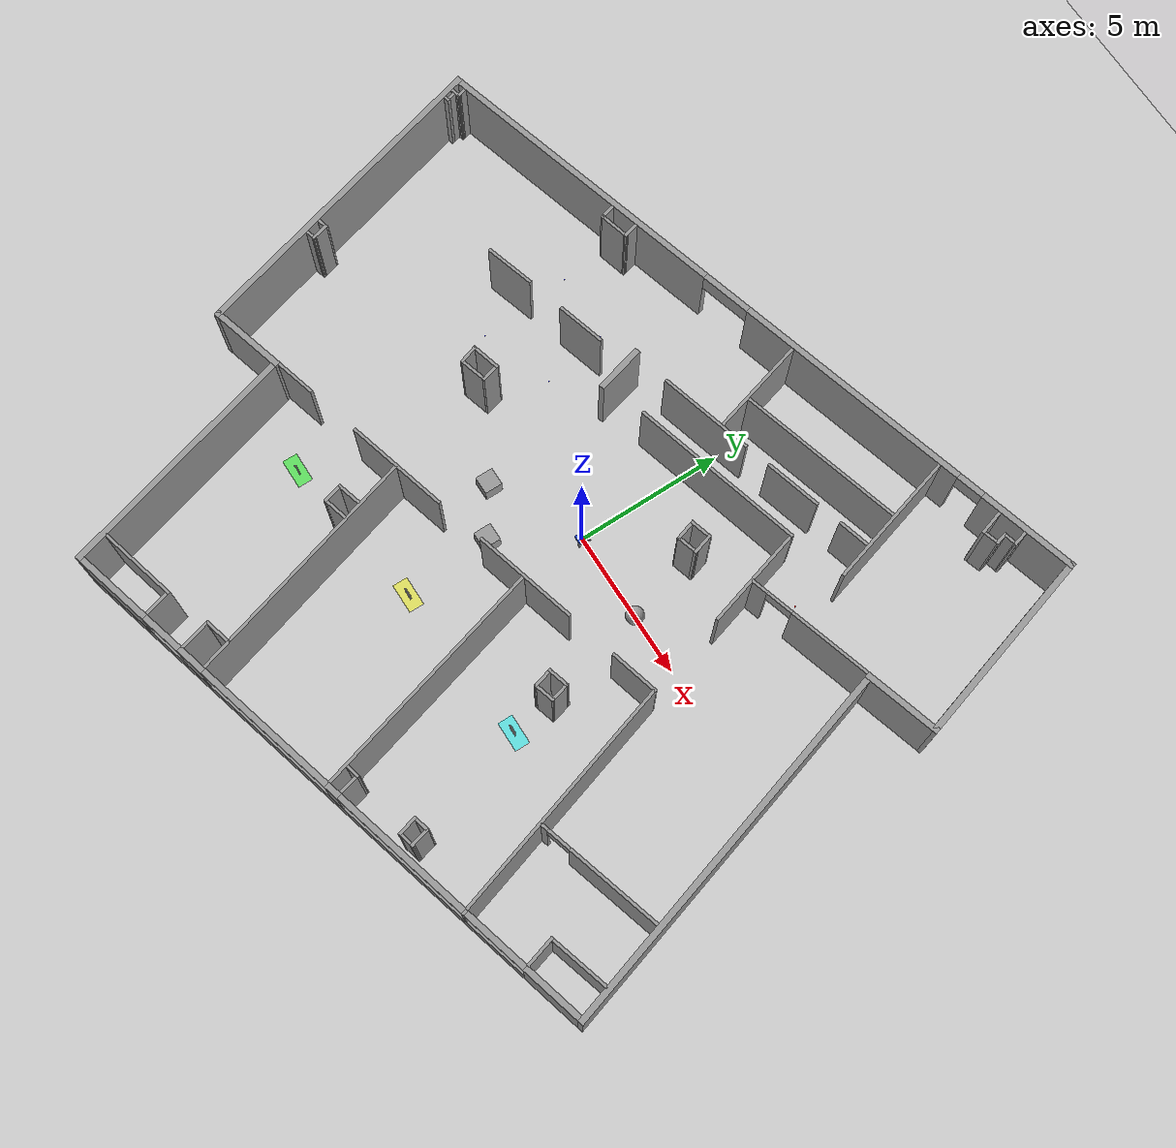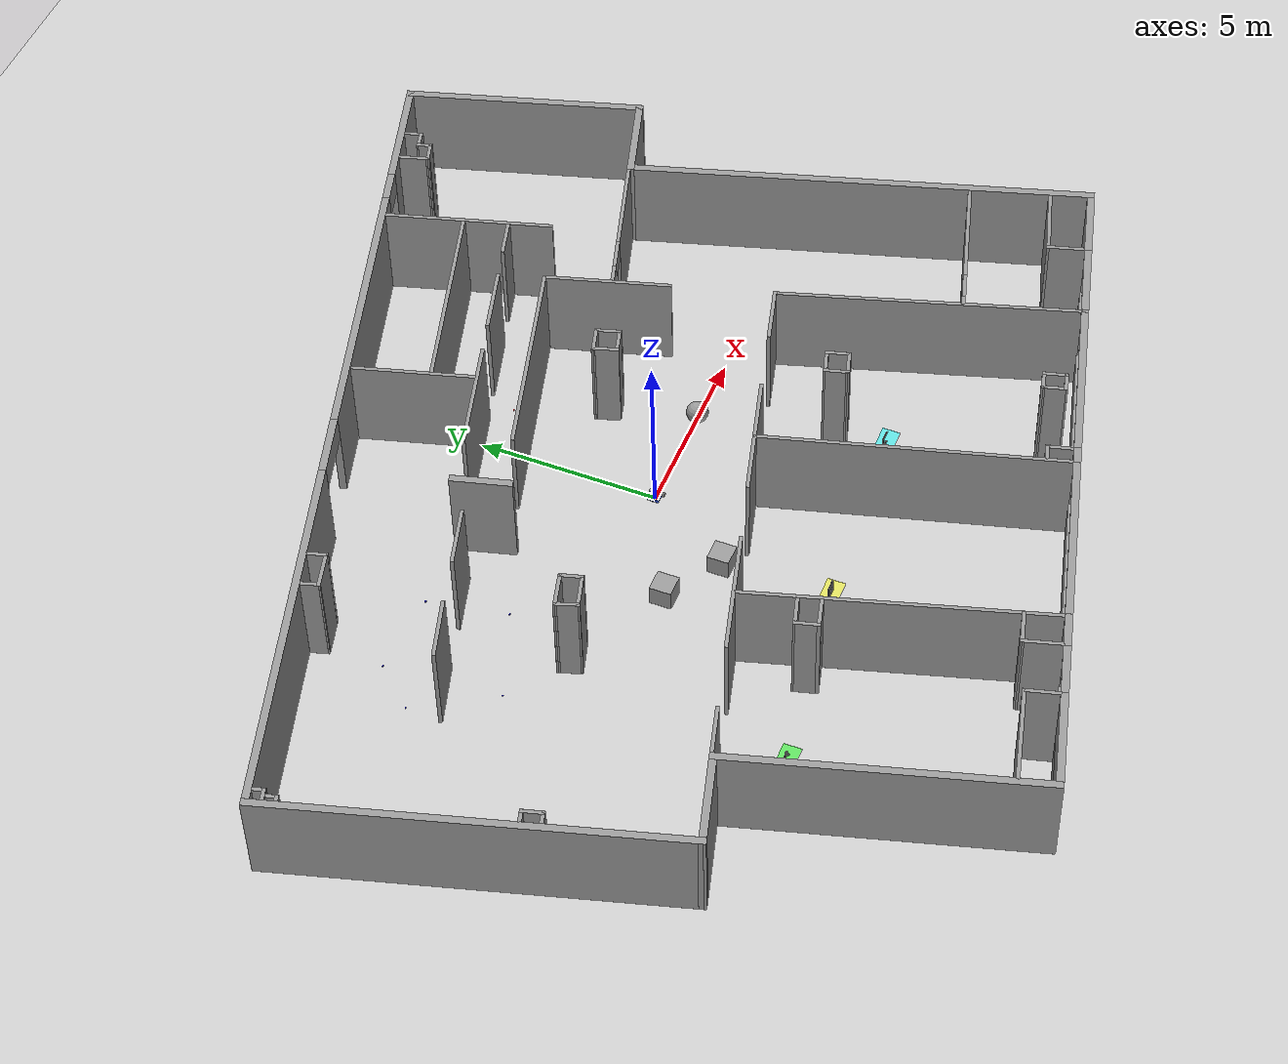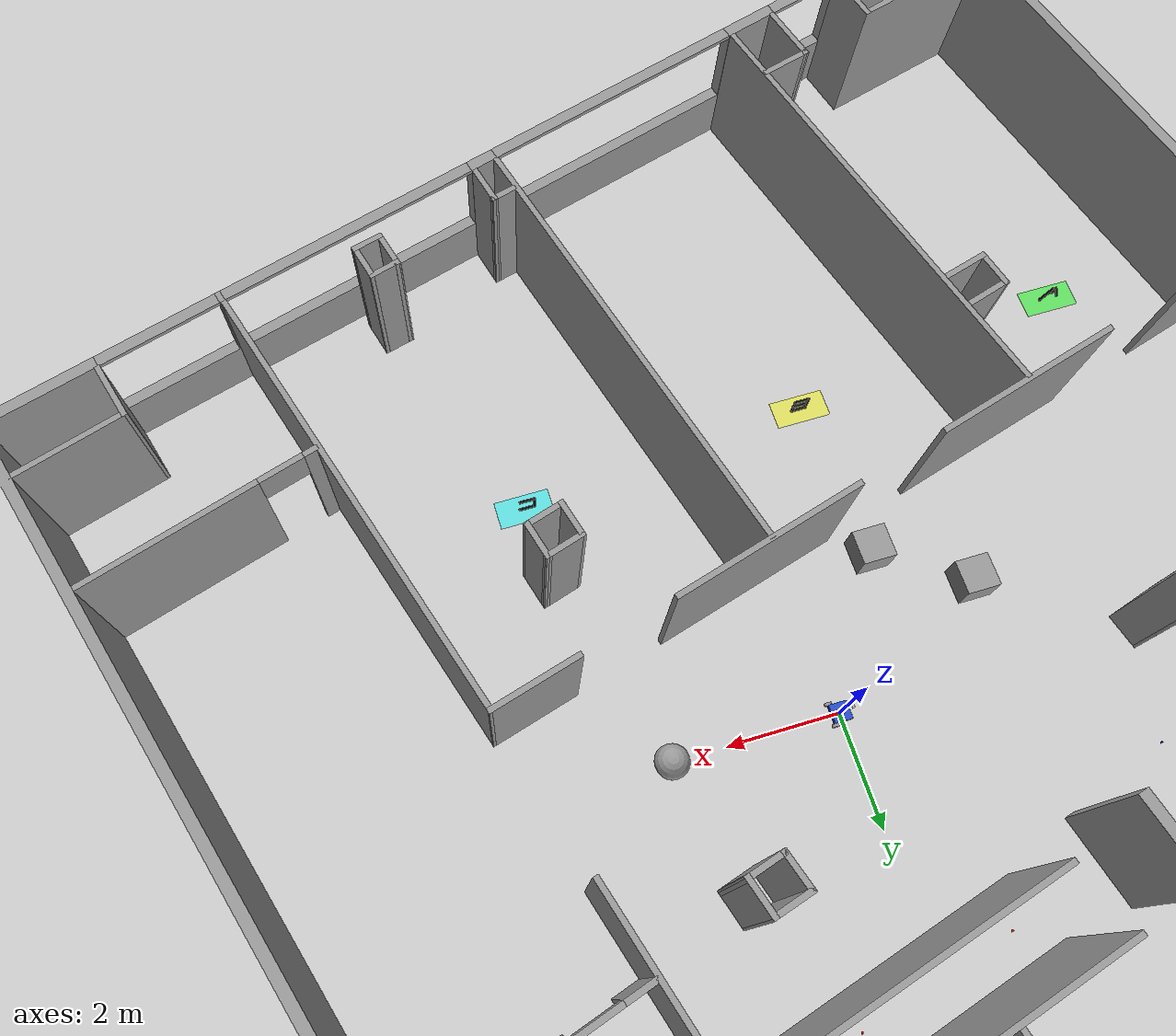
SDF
<sdf version='1.7'>
  <world name='default'>
    <light name='sun' type='directional'>
      <cast_shadows>1</cast_shadows>
      <pose>0 0 10 0 -0 0</pose>
      <diffuse>0.8 0.8 0.8 1</diffuse>
      <specular>0.2 0.2 0.2 1</specular>
      <attenuation>
        <range>1000</range>
        <constant>0.9</constant>
        <linear>0.01</linear>
        <quadratic>0.001</quadratic>
      </attenuation>
      <direction>-0.5 0.1 -0.9</direction>
      <spot>
        <inner_angle>0</inner_angle>
        <outer_angle>0</outer_angle>
        <falloff>0</falloff>
      </spot>
    </light>
    <model name='ground_plane'>
      <static>1</static>
      <link name='link'>
        <collision name='collision'>
          <geometry>
            <plane>
              <normal>0 0 1</normal>
              <size>100 100</size>
            </plane>
          </geometry>
          <surface>
            <friction>
              <ode>
                <mu>100</mu>
                <mu2>50</mu2>
              </ode>
              <torsional>
                <ode/>
              </torsional>
            </friction>
            <bounce/>
            <contact>
              <ode/>
            </contact>
          </surface>
          <max_contacts>10</max_contacts>
        </collision>
        <visual name='visual'>
          <cast_shadows>0</cast_shadows>
          <geometry>
            <plane>
              <normal>0 0 1</normal>
              <size>100 100</size>
            </plane>
          </geometry>
          <material>
            <script>
              <uri>file://media/materials/scripts/gazebo.material</uri>
              <name>Gazebo/Grey</name>
            </script>
          </material>
        </visual>
        <velocity_decay>
          <linear>0</linear>
          <angular>0</angular>
        </velocity_decay>
        <self_collide>0</self_collide>
        <kinematic>0</kinematic>
        <gravity>1</gravity>
        <enable_wind>0</enable_wind>
      </link>
    </model>
    <physics type='ode'>
      <ode>
        <solver>
          <type>quick</type>
          <iters>20</iters>
          <sor>1</sor>
          <use_dynamic_moi_rescaling>0</use_dynamic_moi_rescaling>
        </solver>
        <constraints>
          <cfm>0</cfm>
          <erp>0.2</erp>
          <contact_max_correcting_vel>100</contact_max_correcting_vel>
          <contact_surface_layer>0</contact_surface_layer>
        </constraints>
      </ode>
      <real_time_update_rate>1000</real_time_update_rate>
      <max_step_size>0.001</max_step_size>
      <real_time_factor>1</real_time_factor>
      <max_contacts>20</max_contacts>
    </physics>
    <scene>
      <ambient>0.4 0.4 0.4 1</ambient>
      <background>0.7 0.7 0.7 1</background>
      <shadows>1</shadows>
    </scene>
    <spherical_coordinates>
      <surface_model>EARTH_WGS84</surface_model>
      <latitude_deg>0</latitude_deg>
      <longitude_deg>0</longitude_deg>
      <elevation>0</elevation>
      <heading_deg>0</heading_deg>
    </spherical_coordinates>
    <model name='PAL_office'>
      <pose>-1 -1 0 0 -0 0</pose>
      <link name='Wall_10'>
        <collision name='Wall_10_Collision'>
          <geometry>
            <box>
              <size>6.73478 0.2 2.78</size>
            </box>
          </geometry>
          <pose>0 0 1.39 0 -0 0</pose>
          <max_contacts>10</max_contacts>
          <surface>
            <bounce/>
            <friction>
              <ode/>
              <torsional>
                <ode/>
              </torsional>
            </friction>
            <contact>
              <ode/>
            </contact>
          </surface>
        </collision>
        <visual name='Wall_10_Visual'>
          <pose>0 0 1.39 0 -0 0</pose>
          <geometry>
            <box>
              <size>6.73478 0.2 2.78</size>
            </box>
          </geometry>
          <material>
            <script>
              <uri>file://media/materials/scripts/gazebo.material</uri>
              <name>Gazebo/Grey</name>
            </script>
            <ambient>0.5 0.5 0.5 1</ambient>
          </material>
        </visual>
        <pose>11.1005 9.10601 0 0 -0 1.85624</pose>
        <velocity_decay>
          <linear>0</linear>
          <angular>0</angular>
        </velocity_decay>
        <self_collide>0</self_collide>
        <kinematic>0</kinematic>
        <gravity>1</gravity>
        <enable_wind>0</enable_wind>
      </link>
      <link name='Wall_101'>
        <collision name='Wall_101_Collision'>
          <geometry>
            <box>
              <size>0.35 0.1 2.78</size>
            </box>
          </geometry>
          <pose>0 0 1.39 0 -0 0</pose>
          <max_contacts>10</max_contacts>
          <surface>
            <bounce/>
            <friction>
              <ode/>
              <torsional>
                <ode/>
              </torsional>
            </friction>
            <contact>
              <ode/>
            </contact>
          </surface>
        </collision>
        <visual name='Wall_101_Visual'>
          <pose>0 0 1.39 0 -0 0</pose>
          <geometry>
            <box>
              <size>0.35 0.1 2.78</size>
            </box>
          </geometry>
          <material>
            <script>
              <uri>file://media/materials/scripts/gazebo.material</uri>
              <name>Gazebo/Grey</name>
            </script>
            <ambient>0.5 0.5 0.5 1</ambient>
          </material>
        </visual>
        <pose>-13.001 5.22701 0 0 0 -2.87429</pose>
        <velocity_decay>
          <linear>0</linear>
          <angular>0</angular>
        </velocity_decay>
        <self_collide>0</self_collide>
        <kinematic>0</kinematic>
        <gravity>1</gravity>
        <enable_wind>0</enable_wind>
      </link>
      <link name='Wall_103'>
        <collision name='Wall_103_Collision'>
          <geometry>
            <box>
              <size>0.35 0.1 2.78</size>
            </box>
          </geometry>
          <pose>0 0 1.39 0 -0 0</pose>
          <max_contacts>10</max_contacts>
          <surface>
            <bounce/>
            <friction>
              <ode/>
              <torsional>
                <ode/>
              </torsional>
            </friction>
            <contact>
              <ode/>
            </contact>
          </surface>
        </collision>
        <visual name='Wall_103_Visual'>
          <pose>0 0 1.39 0 -0 0</pose>
          <geometry>
            <box>
              <size>0.35 0.1 2.78</size>
            </box>
          </geometry>
          <material>
            <script>
              <uri>file://media/materials/scripts/gazebo.material</uri>
              <name>Gazebo/Grey</name>
            </script>
            <ambient>0.5 0.5 0.5 1</ambient>
          </material>
        </visual>
        <pose>-12.915 5.38001 0 0 -0 1.85075</pose>
        <velocity_decay>
          <linear>0</linear>
          <angular>0</angular>
        </velocity_decay>
        <self_collide>0</self_collide>
        <kinematic>0</kinematic>
        <gravity>1</gravity>
        <enable_wind>0</enable_wind>
      </link>
      <link name='Wall_113'>
        <collision name='Wall_113_Collision'>
          <geometry>
            <box>
              <size>0.183 0.1 2.78</size>
            </box>
          </geometry>
          <pose>0 0 1.39 0 -0 0</pose>
          <max_contacts>10</max_contacts>
          <surface>
            <bounce/>
            <friction>
              <ode/>
              <torsional>
                <ode/>
              </torsional>
            </friction>
            <contact>
              <ode/>
            </contact>
          </surface>
        </collision>
        <visual name='Wall_113_Visual'>
          <pose>0 0 1.39 0 -0 0</pose>
          <geometry>
            <box>
              <size>0.183 0.1 2.78</size>
            </box>
          </geometry>
          <material>
            <script>
              <uri>file://media/materials/scripts/gazebo.material</uri>
              <name>Gazebo/Grey</name>
            </script>
            <ambient>0.5 0.5 0.5 1</ambient>
          </material>
        </visual>
        <pose>-12.9885 4.88001 0 0 -0 0.268366</pose>
        <velocity_decay>
          <linear>0</linear>
          <angular>0</angular>
        </velocity_decay>
        <self_collide>0</self_collide>
        <kinematic>0</kinematic>
        <gravity>1</gravity>
        <enable_wind>0</enable_wind>
      </link>
      <link name='Wall_118'>
        <collision name='Wall_118_Collision'>
          <geometry>
            <box>
              <size>0.252054 0.1 2.78</size>
            </box>
          </geometry>
          <pose>0 0 1.39 0 -0 0</pose>
          <max_contacts>10</max_contacts>
          <surface>
            <bounce/>
            <friction>
              <ode/>
              <torsional>
                <ode/>
              </torsional>
            </friction>
            <contact>
              <ode/>
            </contact>
          </surface>
        </collision>
        <visual name='Wall_118_Visual'>
          <pose>0 0 1.39 0 -0 0</pose>
          <geometry>
            <box>
              <size>0.252054 0.1 2.78</size>
            </box>
          </geometry>
          <material>
            <script>
              <uri>file://media/materials/scripts/gazebo.material</uri>
              <name>Gazebo/Grey</name>
            </script>
            <ambient>0.5 0.5 0.5 1</ambient>
          </material>
        </visual>
        <pose>-12.996 5.05551 0 0 0 -1.31147</pose>
        <velocity_decay>
          <linear>0</linear>
          <angular>0</angular>
        </velocity_decay>
        <self_collide>0</self_collide>
        <kinematic>0</kinematic>
        <gravity>1</gravity>
        <enable_wind>0</enable_wind>
      </link>
      <link name='Wall_12'>
        <collision name='Wall_12_Collision'>
          <geometry>
            <box>
              <size>2.648 0.2 2.78</size>
            </box>
          </geometry>
          <pose>0 0 1.39 0 -0 0</pose>
          <max_contacts>10</max_contacts>
          <surface>
            <bounce/>
            <friction>
              <ode/>
              <torsional>
                <ode/>
              </torsional>
            </friction>
            <contact>
              <ode/>
            </contact>
          </surface>
        </collision>
        <visual name='Wall_12_Visual'>
          <pose>0 0 1.39 0 -0 0</pose>
          <geometry>
            <box>
              <size>2.648 0.2 2.78</size>
            </box>
          </geometry>
          <material>
            <script>
              <uri>file://media/materials/scripts/gazebo.material</uri>
              <name>Gazebo/Grey</name>
            </script>
            <ambient>0.5 0.5 0.5 1</ambient>
          </material>
        </visual>
        <pose>-9.23199 -4.61199 0 0 0 -2.8652</pose>
        <velocity_decay>
          <linear>0</linear>
          <angular>0</angular>
        </velocity_decay>
        <self_collide>0</self_collide>
        <kinematic>0</kinematic>
        <gravity>1</gravity>
        <enable_wind>0</enable_wind>
      </link>
      <link name='Wall_121'>
        <collision name='Wall_121_Collision'>
          <geometry>
            <box>
              <size>1.01214 0.1 2.78</size>
            </box>
          </geometry>
          <pose>0 0 1.39 0 -0 0</pose>
          <max_contacts>10</max_contacts>
          <surface>
            <bounce/>
            <friction>
              <ode/>
              <torsional>
                <ode/>
              </torsional>
            </friction>
            <contact>
              <ode/>
            </contact>
          </surface>
        </collision>
        <visual name='Wall_121_Visual'>
          <pose>0 0 1.39 0 -0 0</pose>
          <geometry>
            <box>
              <size>1.01214 0.1 2.78</size>
            </box>
          </geometry>
          <material>
            <script>
              <uri>file://media/materials/scripts/gazebo.material</uri>
              <name>Gazebo/Grey</name>
            </script>
            <ambient>0.5 0.5 0.5 1</ambient>
          </material>
        </visual>
        <pose>-4.76149 1.21201 0 0 -0 0.266252</pose>
        <velocity_decay>
          <linear>0</linear>
          <angular>0</angular>
        </velocity_decay>
        <self_collide>0</self_collide>
        <kinematic>0</kinematic>
        <gravity>1</gravity>
        <enable_wind>0</enable_wind>
      </link>
      <link name='Wall_122'>
        <collision name='Wall_122_Collision'>
          <geometry>
            <box>
              <size>0.660446 0.1 2.78</size>
            </box>
          </geometry>
          <pose>0 0 1.39 0 -0 0</pose>
          <max_contacts>10</max_contacts>
          <surface>
            <bounce/>
            <friction>
              <ode/>
              <torsional>
                <ode/>
              </torsional>
            </friction>
            <contact>
              <ode/>
            </contact>
          </surface>
        </collision>
        <visual name='Wall_122_Visual'>
          <pose>0 0 1.39 0 -0 0</pose>
          <geometry>
            <box>
              <size>0.660446 0.1 2.78</size>
            </box>
          </geometry>
          <material>
            <script>
              <uri>file://media/materials/scripts/gazebo.material</uri>
              <name>Gazebo/Grey</name>
            </script>
            <ambient>0.5 0.5 0.5 1</ambient>
          </material>
        </visual>
        <pose>-4.24649 1.06201 0 0 0 -1.29985</pose>
        <velocity_decay>
          <linear>0</linear>
          <angular>0</angular>
        </velocity_decay>
        <self_collide>0</self_collide>
        <kinematic>0</kinematic>
        <gravity>1</gravity>
        <enable_wind>0</enable_wind>
      </link>
      <link name='Wall_127'>
        <collision name='Wall_127_Collision'>
          <geometry>
            <box>
              <size>0.678705 0.1 2.78</size>
            </box>
          </geometry>
          <pose>0 0 1.39 0 -0 0</pose>
          <max_contacts>10</max_contacts>
          <surface>
            <bounce/>
            <friction>
              <ode/>
              <torsional>
                <ode/>
              </torsional>
            </friction>
            <contact>
              <ode/>
            </contact>
          </surface>
        </collision>
        <visual name='Wall_127_Visual'>
          <pose>0 0 1.39 0 -0 0</pose>
          <geometry>
            <box>
              <size>0.678705 0.1 2.78</size>
            </box>
          </geometry>
          <material>
            <script>
              <uri>file://media/materials/scripts/gazebo.material</uri>
              <name>Gazebo/Grey</name>
            </script>
            <ambient>0.5 0.5 0.5 1</ambient>
          </material>
        </visual>
        <pose>-5.11149 0.817011 0 0 0 -1.25451</pose>
        <velocity_decay>
          <linear>0</linear>
          <angular>0</angular>
        </velocity_decay>
        <self_collide>0</self_collide>
        <kinematic>0</kinematic>
        <gravity>1</gravity>
        <enable_wind>0</enable_wind>
      </link>
      <link name='Wall_128'>
        <collision name='Wall_128_Collision'>
          <geometry>
            <box>
              <size>0.913204 0.1 2.78</size>
            </box>
          </geometry>
          <pose>0 0 1.39 0 -0 0</pose>
          <max_contacts>10</max_contacts>
          <surface>
            <bounce/>
            <friction>
              <ode/>
              <torsional>
                <ode/>
              </torsional>
            </friction>
            <contact>
              <ode/>
            </contact>
          </surface>
        </collision>
        <visual name='Wall_128_Visual'>
          <pose>0 0 1.39 0 -0 0</pose>
          <geometry>
            <box>
              <size>0.913204 0.1 2.78</size>
            </box>
          </geometry>
          <material>
            <script>
              <uri>file://media/materials/scripts/gazebo.material</uri>
              <name>Gazebo/Grey</name>
            </script>
            <ambient>0.5 0.5 0.5 1</ambient>
          </material>
        </visual>
        <pose>-4.63149 0.657011 0 0 -0 0.286745</pose>
        <velocity_decay>
          <linear>0</linear>
          <angular>0</angular>
        </velocity_decay>
        <self_collide>0</self_collide>
        <kinematic>0</kinematic>
        <gravity>1</gravity>
        <enable_wind>0</enable_wind>
      </link>
      <link name='Wall_133'>
        <collision name='Wall_133_Collision'>
          <geometry>
            <box>
              <size>0.754498 0.1 2.78</size>
            </box>
          </geometry>
          <pose>0 0 1.39 0 -0 0</pose>
          <max_contacts>10</max_contacts>
          <surface>
            <bounce/>
            <friction>
              <ode/>
              <torsional>
                <ode/>
              </torsional>
            </friction>
            <contact>
              <ode/>
            </contact>
          </surface>
        </collision>
        <visual name='Wall_133_Visual'>
          <pose>0 0 1.39 0 -0 0</pose>
          <geometry>
            <box>
              <size>0.754498 0.1 2.78</size>
            </box>
          </geometry>
          <material>
            <script>
              <uri>file://media/materials/scripts/gazebo.material</uri>
              <name>Gazebo/Grey</name>
            </script>
            <ambient>0.5 0.5 0.5 1</ambient>
          </material>
        </visual>
        <pose>3.37451 3.66401 0 0 -0 0.275362</pose>
        <velocity_decay>
          <linear>0</linear>
          <angular>0</angular>
        </velocity_decay>
        <self_collide>0</self_collide>
        <kinematic>0</kinematic>
        <gravity>1</gravity>
        <enable_wind>0</enable_wind>
      </link>
      <link name='Wall_134'>
        <collision name='Wall_134_Collision'>
          <geometry>
            <box>
              <size>0.726947 0.1 2.78</size>
            </box>
          </geometry>
          <pose>0 0 1.39 0 -0 0</pose>
          <max_contacts>10</max_contacts>
          <surface>
            <bounce/>
            <friction>
              <ode/>
              <torsional>
                <ode/>
              </torsional>
            </friction>
            <contact>
              <ode/>
            </contact>
          </surface>
        </collision>
        <visual name='Wall_134_Visual'>
          <pose>0 0 1.39 0 -0 0</pose>
          <geometry>
            <box>
              <size>0.726947 0.1 2.78</size>
            </box>
          </geometry>
          <material>
            <script>
              <uri>file://media/materials/scripts/gazebo.material</uri>
              <name>Gazebo/Grey</name>
            </script>
            <ambient>0.5 0.5 0.5 1</ambient>
          </material>
        </visual>
        <pose>3.77951 3.45301 0 0 0 -1.27934</pose>
        <velocity_decay>
          <linear>0</linear>
          <angular>0</angular>
        </velocity_decay>
        <self_collide>0</self_collide>
        <kinematic>0</kinematic>
        <gravity>1</gravity>
        <enable_wind>0</enable_wind>
      </link>
      <link name='Wall_14'>
        <collision name='Wall_14_Collision'>
          <geometry>
            <box>
              <size>8.475 0.2 2.78</size>
            </box>
          </geometry>
          <pose>0 0 1.39 0 -0 0</pose>
          <max_contacts>10</max_contacts>
          <surface>
            <bounce/>
            <friction>
              <ode/>
              <torsional>
                <ode/>
              </torsional>
            </friction>
            <contact>
              <ode/>
            </contact>
          </surface>
        </collision>
        <visual name='Wall_14_Visual'>
          <pose>0 0 1.39 0 -0 0</pose>
          <geometry>
            <box>
              <size>8.475 0.2 2.78</size>
            </box>
          </geometry>
          <material>
            <script>
              <uri>file://media/materials/scripts/gazebo.material</uri>
              <name>Gazebo/Grey</name>
            </script>
            <ambient>0.5 0.5 0.5 1</ambient>
          </material>
        </visual>
        <pose>-6.93049 -8.25999 0 0 0 -1.29568</pose>
        <velocity_decay>
          <linear>0</linear>
          <angular>0</angular>
        </velocity_decay>
        <self_collide>0</self_collide>
        <kinematic>0</kinematic>
        <gravity>1</gravity>
        <enable_wind>0</enable_wind>
      </link>
      <link name='Wall_140'>
        <collision name='Wall_140_Collision'>
          <geometry>
            <box>
              <size>0.729033 0.1 2.78</size>
            </box>
          </geometry>
          <pose>0 0 1.39 0 -0 0</pose>
          <max_contacts>10</max_contacts>
          <surface>
            <bounce/>
            <friction>
              <ode/>
              <torsional>
                <ode/>
              </torsional>
            </friction>
            <contact>
              <ode/>
            </contact>
          </surface>
        </collision>
        <visual name='Wall_140_Visual'>
          <pose>0 0 1.39 0 -0 0</pose>
          <geometry>
            <box>
              <size>0.729033 0.1 2.78</size>
            </box>
          </geometry>
          <material>
            <script>
              <uri>file://media/materials/scripts/gazebo.material</uri>
              <name>Gazebo/Grey</name>
            </script>
            <ambient>0.5 0.5 0.5 1</ambient>
          </material>
        </visual>
        <pose>3.15251 3.27451 0 0 0 -1.27066</pose>
        <velocity_decay>
          <linear>0</linear>
          <angular>0</angular>
        </velocity_decay>
        <self_collide>0</self_collide>
        <kinematic>0</kinematic>
        <gravity>1</gravity>
        <enable_wind>0</enable_wind>
      </link>
      <link name='Wall_142'>
        <collision name='Wall_142_Collision'>
          <geometry>
            <box>
              <size>0.721105 0.1 2.78</size>
            </box>
          </geometry>
          <pose>0 0 1.39 0 -0 0</pose>
          <max_contacts>10</max_contacts>
          <surface>
            <bounce/>
            <friction>
              <ode/>
              <torsional>
                <ode/>
              </torsional>
            </friction>
            <contact>
              <ode/>
            </contact>
          </surface>
        </collision>
        <visual name='Wall_142_Visual'>
          <pose>0 0 1.39 0 -0 0</pose>
          <geometry>
            <box>
              <size>0.721105 0.1 2.78</size>
            </box>
          </geometry>
          <material>
            <script>
              <uri>file://media/materials/scripts/gazebo.material</uri>
              <name>Gazebo/Grey</name>
            </script>
            <ambient>0.5 0.5 0.5 1</ambient>
          </material>
        </visual>
        <pose>3.57151 3.06601 0 0 0 -2.85754</pose>
        <velocity_decay>
          <linear>0</linear>
          <angular>0</angular>
        </velocity_decay>
        <self_collide>0</self_collide>
        <kinematic>0</kinematic>
        <gravity>1</gravity>
        <enable_wind>0</enable_wind>
      </link>
      <link name='Wall_145'>
        <collision name='Wall_145_Collision'>
          <geometry>
            <box>
              <size>8.27375 0.1 2.78</size>
            </box>
          </geometry>
          <pose>0 0 1.39 0 -0 0</pose>
          <max_contacts>10</max_contacts>
          <surface>
            <bounce/>
            <friction>
              <ode/>
              <torsional>
                <ode/>
              </torsional>
            </friction>
            <contact>
              <ode/>
            </contact>
          </surface>
        </collision>
        <visual name='Wall_145_Visual'>
          <pose>0 0 1.39 0 -0 0</pose>
          <geometry>
            <box>
              <size>8.27375 0.1 2.78</size>
            </box>
          </geometry>
          <material>
            <script>
              <uri>file://media/materials/scripts/gazebo.material</uri>
              <name>Gazebo/Grey</name>
            </script>
            <ambient>0.5 0.5 0.5 1</ambient>
          </material>
        </visual>
        <pose>7.88901 -4.08549 0 0 0 -1.27598</pose>
        <velocity_decay>
          <linear>0</linear>
          <angular>0</angular>
        </velocity_decay>
        <self_collide>0</self_collide>
        <kinematic>0</kinematic>
        <gravity>1</gravity>
        <enable_wind>0</enable_wind>
      </link>
      <link name='Wall_147'>
        <collision name='Wall_147_Collision'>
          <geometry>
            <box>
              <size>1.6624 0.1 2.78</size>
            </box>
          </geometry>
          <pose>0 0 1.39 0 -0 0</pose>
          <max_contacts>10</max_contacts>
          <surface>
            <bounce/>
            <friction>
              <ode/>
              <torsional>
                <ode/>
              </torsional>
            </friction>
            <contact>
              <ode/>
            </contact>
          </surface>
        </collision>
        <visual name='Wall_147_Visual'>
          <pose>0 0 1.39 0 -0 0</pose>
          <geometry>
            <box>
              <size>1.6624 0.1 2.78</size>
            </box>
          </geometry>
          <material>
            <script>
              <uri>file://media/materials/scripts/gazebo.material</uri>
              <name>Gazebo/Grey</name>
            </script>
            <ambient>0.5 0.5 0.5 1</ambient>
          </material>
        </visual>
        <pose>5.94751 -0.379989 0 0 0 -2.87613</pose>
        <velocity_decay>
          <linear>0</linear>
          <angular>0</angular>
        </velocity_decay>
        <self_collide>0</self_collide>
        <kinematic>0</kinematic>
        <gravity>1</gravity>
        <enable_wind>0</enable_wind>
      </link>
      <link name='Wall_150'>
        <pose>10.26 -4.39249 0 0 -0 0.289894</pose>
        <visual name='Wall_150_Visual_0'>
          <pose>-2.03127 0 1.39 0 -0 0</pose>
          <geometry>
            <box>
              <size>0.2671 0.1 2.78</size>
            </box>
          </geometry>
          <material>
            <script>
              <uri>file://media/materials/scripts/gazebo.material</uri>
              <name>Gazebo/Grey</name>
            </script>
            <ambient>0.5 0.5 0.5 1</ambient>
          </material>
        </visual>
        <collision name='Wall_150_Collision_0'>
          <geometry>
            <box>
              <size>0.2671 0.1 2.78</size>
            </box>
          </geometry>
          <pose>-2.03127 0 1.39 0 -0 0</pose>
          <max_contacts>10</max_contacts>
          <surface>
            <bounce/>
            <friction>
              <ode/>
              <torsional>
                <ode/>
              </torsional>
            </friction>
            <contact>
              <ode/>
            </contact>
          </surface>
        </collision>
        <visual name='Wall_150_Visual_1'>
          <pose>0.54355 0 1.39 0 -0 0</pose>
          <geometry>
            <box>
              <size>3.24255 0.1 2.78</size>
            </box>
          </geometry>
          <material>
            <script>
              <uri>file://media/materials/scripts/gazebo.material</uri>
              <name>Gazebo/Grey</name>
            </script>
            <ambient>0.5 0.5 0.5 1</ambient>
          </material>
        </visual>
        <collision name='Wall_150_Collision_1'>
          <geometry>
            <box>
              <size>3.24255 0.1 2.78</size>
            </box>
          </geometry>
          <pose>0.54355 0 1.39 0 -0 0</pose>
          <max_contacts>10</max_contacts>
          <surface>
            <bounce/>
            <friction>
              <ode/>
              <torsional>
                <ode/>
              </torsional>
            </friction>
            <contact>
              <ode/>
            </contact>
          </surface>
        </collision>
        <visual name='Wall_150_Visual_2'>
          <pose>-1.48772 0 2.44 0 -0 0</pose>
          <geometry>
            <box>
              <size>0.82 0.1 0.68</size>
            </box>
          </geometry>
          <material>
            <script>
              <uri>file://media/materials/scripts/gazebo.material</uri>
              <name>Gazebo/Grey</name>
            </script>
            <ambient>0.5 0.5 0.5 1</ambient>
          </material>
        </visual>
        <collision name='Wall_150_Collision_2'>
          <geometry>
            <box>
              <size>0.82 0.1 0.68</size>
            </box>
          </geometry>
          <pose>-1.48772 0 2.44 0 -0 0</pose>
          <max_contacts>10</max_contacts>
          <surface>
            <bounce/>
            <friction>
              <ode/>
              <torsional>
                <ode/>
              </torsional>
            </friction>
            <contact>
              <ode/>
            </contact>
          </surface>
        </collision>
        <velocity_decay>
          <linear>0</linear>
          <angular>0</angular>
        </velocity_decay>
        <self_collide>0</self_collide>
        <kinematic>0</kinematic>
        <gravity>1</gravity>
        <enable_wind>0</enable_wind>
      </link>
      <link name='Wall_153'>
        <collision name='Wall_153_Collision'>
          <geometry>
            <box>
              <size>2.08407 0.1 2.78</size>
            </box>
          </geometry>
          <pose>0 0 1.39 0 -0 0</pose>
          <max_contacts>10</max_contacts>
          <surface>
            <bounce/>
            <friction>
              <ode/>
              <torsional>
                <ode/>
              </torsional>
            </friction>
            <contact>
              <ode/>
            </contact>
          </surface>
        </collision>
        <visual name='Wall_153_Visual'>
          <pose>0 0 1.39 0 -0 0</pose>
          <geometry>
            <box>
              <size>2.08407 0.1 2.78</size>
            </box>
          </geometry>
          <material>
            <script>
              <uri>file://media/materials/scripts/gazebo.material</uri>
              <name>Gazebo/Grey</name>
            </script>
            <ambient>0.5 0.5 0.5 1</ambient>
          </material>
        </visual>
        <pose>11.9955 -6.18599 0 0 0 -2.85014</pose>
        <velocity_decay>
          <linear>0</linear>
          <angular>0</angular>
        </velocity_decay>
        <self_collide>0</self_collide>
        <kinematic>0</kinematic>
        <gravity>1</gravity>
        <enable_wind>0</enable_wind>
      </link>
      <link name='Wall_154'>
        <collision name='Wall_154_Collision'>
          <geometry>
            <box>
              <size>1.04397 0.1 2.78</size>
            </box>
          </geometry>
          <pose>0 0 1.39 0 -0 0</pose>
          <max_contacts>10</max_contacts>
          <surface>
            <bounce/>
            <friction>
              <ode/>
              <torsional>
                <ode/>
              </torsional>
            </friction>
            <contact>
              <ode/>
            </contact>
          </surface>
        </collision>
        <visual name='Wall_154_Visual'>
          <pose>0 0 1.39 0 -0 0</pose>
          <geometry>
            <box>
              <size>1.04397 0.1 2.78</size>
            </box>
          </geometry>
          <material>
            <script>
              <uri>file://media/materials/scripts/gazebo.material</uri>
              <name>Gazebo/Grey</name>
            </script>
            <ambient>0.5 0.5 0.5 1</ambient>
          </material>
        </visual>
        <pose>11.176 -6.92449 0 0 0 -1.29061</pose>
        <velocity_decay>
          <linear>0</linear>
          <angular>0</angular>
        </velocity_decay>
        <self_collide>0</self_collide>
        <kinematic>0</kinematic>
        <gravity>1</gravity>
        <enable_wind>0</enable_wind>
      </link>
      <link name='Wall_158'>
        <collision name='Wall_158_Collision'>
          <geometry>
            <box>
              <size>3.52366 0.1 2.78</size>
            </box>
          </geometry>
          <pose>0 0 1.39 0 -0 0</pose>
          <max_contacts>10</max_contacts>
          <surface>
            <bounce/>
            <friction>
              <ode/>
              <torsional>
                <ode/>
              </torsional>
            </friction>
            <contact>
              <ode/>
            </contact>
          </surface>
        </collision>
        <visual name='Wall_158_Visual'>
          <pose>0 0 1.39 0 -0 0</pose>
          <geometry>
            <box>
              <size>3.52366 0.1 2.78</size>
            </box>
          </geometry>
          <material>
            <script>
              <uri>file://media/materials/scripts/gazebo.material</uri>
              <name>Gazebo/Grey</name>
            </script>
            <ambient>0.5 0.5 0.5 1</ambient>
          </material>
        </visual>
        <pose>-3.20649 -2.89249 0 0 -0 0.269352</pose>
        <velocity_decay>
          <linear>0</linear>
          <angular>0</angular>
        </velocity_decay>
        <self_collide>0</self_collide>
        <kinematic>0</kinematic>
        <gravity>1</gravity>
        <enable_wind>0</enable_wind>
      </link>
      <link name='Wall_16'>
        <pose>3.78351 -9.59399 0 0 0 -2.87199</pose>
        <visual name='Wall_16_Visual_0'>
          <pose>-8.83974 0 1.39 0 -0 0</pose>
          <geometry>
            <box>
              <size>2.04382 0.2 2.78</size>
            </box>
          </geometry>
          <material>
            <script>
              <uri>file://media/materials/scripts/gazebo.material</uri>
              <name>Gazebo/Grey</name>
            </script>
            <ambient>0.5 0.5 0.5 1</ambient>
          </material>
        </visual>
        <collision name='Wall_16_Collision_0'>
          <geometry>
            <box>
              <size>2.04382 0.2 2.78</size>
            </box>
          </geometry>
          <pose>-8.83974 0 1.39 0 -0 0</pose>
          <max_contacts>10</max_contacts>
          <surface>
            <bounce/>
            <friction>
              <ode/>
              <torsional>
                <ode/>
              </torsional>
            </friction>
            <contact>
              <ode/>
            </contact>
          </surface>
        </collision>
        <visual name='Wall_16_Visual_1'>
          <pose>1.02191 0 0.55 0 -0 0</pose>
          <geometry>
            <box>
              <size>17.6795 0.2 1.1</size>
            </box>
          </geometry>
          <material>
            <script>
              <uri>file://media/materials/scripts/gazebo.material</uri>
              <name>Gazebo/Grey</name>
            </script>
            <ambient>0.5 0.5 0.5 1</ambient>
          </material>
        </visual>
        <collision name='Wall_16_Collision_1'>
          <geometry>
            <box>
              <size>17.6795 0.2 1.1</size>
            </box>
          </geometry>
          <pose>1.02191 0 0.55 0 -0 0</pose>
          <max_contacts>10</max_contacts>
          <surface>
            <bounce/>
            <friction>
              <ode/>
              <torsional>
                <ode/>
              </torsional>
            </friction>
            <contact>
              <ode/>
            </contact>
          </surface>
        </collision>
        <visual name='Wall_16_Visual_2'>
          <pose>-5.54535 0 1.94 0 -0 0</pose>
          <geometry>
            <box>
              <size>0.100368 0.2 1.68</size>
            </box>
          </geometry>
          <material>
            <script>
              <uri>file://media/materials/scripts/gazebo.material</uri>
              <name>Gazebo/Grey</name>
            </script>
            <ambient>0.5 0.5 0.5 1</ambient>
          </material>
        </visual>
        <collision name='Wall_16_Collision_2'>
          <geometry>
            <box>
              <size>0.100368 0.2 1.68</size>
            </box>
          </geometry>
          <pose>-5.54535 0 1.94 0 -0 0</pose>
          <max_contacts>10</max_contacts>
          <surface>
            <bounce/>
            <friction>
              <ode/>
              <torsional>
                <ode/>
              </torsional>
            </friction>
            <contact>
              <ode/>
            </contact>
          </surface>
        </collision>
        <visual name='Wall_16_Visual_3'>
          <pose>-0.435842 0 1.94 0 -0 0</pose>
          <geometry>
            <box>
              <size>0.509797 0.2 1.68</size>
            </box>
          </geometry>
          <material>
            <script>
              <uri>file://media/materials/scripts/gazebo.material</uri>
              <name>Gazebo/Grey</name>
            </script>
            <ambient>0.5 0.5 0.5 1</ambient>
          </material>
        </visual>
        <collision name='Wall_16_Collision_3'>
          <geometry>
            <box>
              <size>0.509797 0.2 1.68</size>
            </box>
          </geometry>
          <pose>-0.435842 0 1.94 0 -0 0</pose>
          <max_contacts>10</max_contacts>
          <surface>
            <bounce/>
            <friction>
              <ode/>
              <torsional>
                <ode/>
              </torsional>
            </friction>
            <contact>
              <ode/>
            </contact>
          </surface>
        </collision>
        <visual name='Wall_16_Visual_4'>
          <pose>5.27686 0 1.94 0 -0 0</pose>
          <geometry>
            <box>
              <size>0.994619 0.2 1.68</size>
            </box>
          </geometry>
          <material>
            <script>
              <uri>file://media/materials/scripts/gazebo.material</uri>
              <name>Gazebo/Grey</name>
            </script>
            <ambient>0.5 0.5 0.5 1</ambient>
          </material>
        </visual>
        <collision name='Wall_16_Collision_4'>
          <geometry>
            <box>
              <size>0.994619 0.2 1.68</size>
            </box>
          </geometry>
          <pose>5.27686 0 1.94 0 -0 0</pose>
          <max_contacts>10</max_contacts>
          <surface>
            <bounce/>
            <friction>
              <ode/>
              <torsional>
                <ode/>
              </torsional>
            </friction>
            <contact>
              <ode/>
            </contact>
          </surface>
        </collision>
        <visual name='Wall_16_Visual_5'>
          <pose>8.53741 0 1.94 0 -0 0</pose>
          <geometry>
            <box>
              <size>2.64848 0.2 1.68</size>
            </box>
          </geometry>
          <material>
            <script>
              <uri>file://media/materials/scripts/gazebo.material</uri>
              <name>Gazebo/Grey</name>
            </script>
            <ambient>0.5 0.5 0.5 1</ambient>
          </material>
        </visual>
        <collision name='Wall_16_Collision_5'>
          <geometry>
            <box>
              <size>2.64848 0.2 1.68</size>
            </box>
          </geometry>
          <pose>8.53741 0 1.94 0 -0 0</pose>
          <max_contacts>10</max_contacts>
          <surface>
            <bounce/>
            <friction>
              <ode/>
              <torsional>
                <ode/>
              </torsional>
            </friction>
            <contact>
              <ode/>
            </contact>
          </surface>
        </collision>
        <visual name='Wall_16_Visual_6'>
          <pose>-6.70668 0 2.74 0 -0 0</pose>
          <geometry>
            <box>
              <size>2.22229 0.2 0.08</size>
            </box>
          </geometry>
          <material>
            <script>
              <uri>file://media/materials/scripts/gazebo.material</uri>
              <name>Gazebo/Grey</name>
            </script>
            <ambient>0.5 0.5 0.5 1</ambient>
          </material>
        </visual>
        <collision name='Wall_16_Collision_6'>
          <geometry>
            <box>
              <size>2.22229 0.2 0.08</size>
            </box>
          </geometry>
          <pose>-6.70668 0 2.74 0 -0 0</pose>
          <max_contacts>10</max_contacts>
          <surface>
            <bounce/>
            <friction>
              <ode/>
              <torsional>
                <ode/>
              </torsional>
            </friction>
            <contact>
              <ode/>
            </contact>
          </surface>
        </collision>
        <visual name='Wall_16_Visual_7'>
          <pose>-3.09295 0 2.74 0 -0 0</pose>
          <geometry>
            <box>
              <size>4.80443 0.2 0.08</size>
            </box>
          </geometry>
          <material>
            <script>
              <uri>file://media/materials/scripts/gazebo.material</uri>
              <name>Gazebo/Grey</name>
            </script>
            <ambient>0.5 0.5 0.5 1</ambient>
          </material>
        </visual>
        <collision name='Wall_16_Collision_7'>
          <geometry>
            <box>
              <size>4.80443 0.2 0.08</size>
            </box>
          </geometry>
          <pose>-3.09295 0 2.74 0 -0 0</pose>
          <max_contacts>10</max_contacts>
          <surface>
            <bounce/>
            <friction>
              <ode/>
              <torsional>
                <ode/>
              </torsional>
            </friction>
            <contact>
              <ode/>
            </contact>
          </surface>
        </collision>
        <visual name='Wall_16_Visual_8'>
          <pose>2.2993 0 2.74 0 -0 0</pose>
          <geometry>
            <box>
              <size>4.96049 0.2 0.08</size>
            </box>
          </geometry>
          <material>
            <script>
              <uri>file://media/materials/scripts/gazebo.material</uri>
              <name>Gazebo/Grey</name>
            </script>
            <ambient>0.5 0.5 0.5 1</ambient>
          </material>
        </visual>
        <collision name='Wall_16_Collision_8'>
          <geometry>
            <box>
              <size>4.96049 0.2 0.08</size>
            </box>
          </geometry>
          <pose>2.2993 0 2.74 0 -0 0</pose>
          <max_contacts>10</max_contacts>
          <surface>
            <bounce/>
            <friction>
              <ode/>
              <torsional>
                <ode/>
              </torsional>
            </friction>
            <contact>
              <ode/>
            </contact>
          </surface>
        </collision>
        <visual name='Wall_16_Visual_9'>
          <pose>6.49367 0 2.74 0 -0 0</pose>
          <geometry>
            <box>
              <size>1.439 0.2 0.08</size>
            </box>
          </geometry>
          <material>
            <script>
              <uri>file://media/materials/scripts/gazebo.material</uri>
              <name>Gazebo/Grey</name>
            </script>
            <ambient>0.5 0.5 0.5 1</ambient>
          </material>
        </visual>
        <collision name='Wall_16_Collision_9'>
          <geometry>
            <box>
              <size>1.439 0.2 0.08</size>
            </box>
          </geometry>
          <pose>6.49367 0 2.74 0 -0 0</pose>
          <max_contacts>10</max_contacts>
          <surface>
            <bounce/>
            <friction>
              <ode/>
              <torsional>
                <ode/>
              </torsional>
            </friction>
            <contact>
              <ode/>
            </contact>
          </surface>
        </collision>
        <velocity_decay>
          <linear>0</linear>
          <angular>0</angular>
        </velocity_decay>
        <self_collide>0</self_collide>
        <kinematic>0</kinematic>
        <gravity>1</gravity>
        <enable_wind>0</enable_wind>
      </link>
      <link name='Wall_160'>
        <collision name='Wall_160_Collision'>
          <geometry>
            <box>
              <size>3.56369 0.1 2.78</size>
            </box>
          </geometry>
          <pose>0 0 1.39 0 -0 0</pose>
          <max_contacts>10</max_contacts>
          <surface>
            <bounce/>
            <friction>
              <ode/>
              <torsional>
                <ode/>
              </torsional>
            </friction>
            <contact>
              <ode/>
            </contact>
          </surface>
        </collision>
        <visual name='Wall_160_Visual'>
          <pose>0 0 1.39 0 -0 0</pose>
          <geometry>
            <box>
              <size>3.56369 0.1 2.78</size>
            </box>
          </geometry>
          <material>
            <script>
              <uri>file://media/materials/scripts/gazebo.material</uri>
              <name>Gazebo/Grey</name>
            </script>
            <ambient>0.5 0.5 0.5 1</ambient>
          </material>
        </visual>
        <pose>1.79301 -1.50349 0 0 -0 0.269139</pose>
        <velocity_decay>
          <linear>0</linear>
          <angular>0</angular>
        </velocity_decay>
        <self_collide>0</self_collide>
        <kinematic>0</kinematic>
        <gravity>1</gravity>
        <enable_wind>0</enable_wind>
      </link>
      <link name='Wall_162'>
        <collision name='Wall_162_Collision'>
          <geometry>
            <box>
              <size>1.39174 0.1 2.78</size>
            </box>
          </geometry>
          <pose>0 0 1.39 0 -0 0</pose>
          <max_contacts>10</max_contacts>
          <surface>
            <bounce/>
            <friction>
              <ode/>
              <torsional>
                <ode/>
              </torsional>
            </friction>
            <contact>
              <ode/>
            </contact>
          </surface>
        </collision>
        <visual name='Wall_162_Visual'>
          <pose>0 0 1.39 0 -0 0</pose>
          <geometry>
            <box>
              <size>1.39174 0.1 2.78</size>
            </box>
          </geometry>
          <material>
            <script>
              <uri>file://media/materials/scripts/gazebo.material</uri>
              <name>Gazebo/Grey</name>
            </script>
            <ambient>0.5 0.5 0.5 1</ambient>
          </material>
        </visual>
        <pose>-7.30849 -4.02049 0 0 0 -2.86808</pose>
        <velocity_decay>
          <linear>0</linear>
          <angular>0</angular>
        </velocity_decay>
        <self_collide>0</self_collide>
        <kinematic>0</kinematic>
        <gravity>1</gravity>
        <enable_wind>0</enable_wind>
      </link>
      <link name='Wall_164'>
        <collision name='Wall_164_Collision'>
          <geometry>
            <box>
              <size>8.25895 0.1 2.78</size>
            </box>
          </geometry>
          <pose>0 0 1.39 0 -0 0</pose>
          <max_contacts>10</max_contacts>
          <surface>
            <bounce/>
            <friction>
              <ode/>
              <torsional>
                <ode/>
              </torsional>
            </friction>
            <contact>
              <ode/>
            </contact>
          </surface>
        </collision>
        <visual name='Wall_164_Visual'>
          <pose>0 0 1.39 0 -0 0</pose>
          <geometry>
            <box>
              <size>8.25895 0.1 2.78</size>
            </box>
          </geometry>
          <material>
            <script>
              <uri>file://media/materials/scripts/gazebo.material</uri>
              <name>Gazebo/Grey</name>
            </script>
            <ambient>0.5 0.5 0.5 1</ambient>
          </material>
        </visual>
        <pose>2.85601 -5.47899 0 0 0 -1.3012</pose>
        <velocity_decay>
          <linear>0</linear>
          <angular>0</angular>
        </velocity_decay>
        <self_collide>0</self_collide>
        <kinematic>0</kinematic>
        <gravity>1</gravity>
        <enable_wind>0</enable_wind>
      </link>
      <link name='Wall_166'>
        <collision name='Wall_166_Collision'>
          <geometry>
            <box>
              <size>8.22 0.1 2.78</size>
            </box>
          </geometry>
          <pose>0 0 1.39 0 -0 0</pose>
          <max_contacts>10</max_contacts>
          <surface>
            <bounce/>
            <friction>
              <ode/>
              <torsional>
                <ode/>
              </torsional>
            </friction>
            <contact>
              <ode/>
            </contact>
          </surface>
        </collision>
        <visual name='Wall_166_Visual'>
          <pose>0 0 1.39 0 -0 0</pose>
          <geometry>
            <box>
              <size>8.22 0.1 2.78</size>
            </box>
          </geometry>
          <material>
            <script>
              <uri>file://media/materials/scripts/gazebo.material</uri>
              <name>Gazebo/Grey</name>
            </script>
            <ambient>0.5 0.5 0.5 1</ambient>
          </material>
        </visual>
        <pose>-2.06049 -6.85199 0 0 0 -1.28668</pose>
        <velocity_decay>
          <linear>0</linear>
          <angular>0</angular>
        </velocity_decay>
        <self_collide>0</self_collide>
        <kinematic>0</kinematic>
        <gravity>1</gravity>
        <enable_wind>0</enable_wind>
      </link>
      <link name='Wall_168'>
        <collision name='Wall_168_Collision'>
          <geometry>
            <box>
              <size>0.743567 0.1 2.78</size>
            </box>
          </geometry>
          <pose>0 0 1.39 0 -0 0</pose>
          <max_contacts>10</max_contacts>
          <surface>
            <bounce/>
            <friction>
              <ode/>
              <torsional>
                <ode/>
              </torsional>
            </friction>
            <contact>
              <ode/>
            </contact>
          </surface>
        </collision>
        <visual name='Wall_168_Visual'>
          <pose>0 0 1.39 0 -0 0</pose>
          <geometry>
            <box>
              <size>0.743567 0.1 2.78</size>
            </box>
          </geometry>
          <material>
            <script>
              <uri>file://media/materials/scripts/gazebo.material</uri>
              <name>Gazebo/Grey</name>
            </script>
            <ambient>0.5 0.5 0.5 1</ambient>
          </material>
        </visual>
        <pose>4.88801 -2.31549 0 0 -0 0.288331</pose>
        <velocity_decay>
          <linear>0</linear>
          <angular>0</angular>
        </velocity_decay>
        <self_collide>0</self_collide>
        <kinematic>0</kinematic>
        <gravity>1</gravity>
        <enable_wind>0</enable_wind>
      </link>
      <link name='Wall_169'>
        <collision name='Wall_169_Collision'>
          <geometry>
            <box>
              <size>0.700613 0.1 2.78</size>
            </box>
          </geometry>
          <pose>0 0 1.39 0 -0 0</pose>
          <max_contacts>10</max_contacts>
          <surface>
            <bounce/>
            <friction>
              <ode/>
              <torsional>
                <ode/>
              </torsional>
            </friction>
            <contact>
              <ode/>
            </contact>
          </surface>
        </collision>
        <visual name='Wall_169_Visual'>
          <pose>0 0 1.39 0 -0 0</pose>
          <geometry>
            <box>
              <size>0.700613 0.1 2.78</size>
            </box>
          </geometry>
          <material>
            <script>
              <uri>file://media/materials/scripts/gazebo.material</uri>
              <name>Gazebo/Grey</name>
            </script>
            <ambient>0.5 0.5 0.5 1</ambient>
          </material>
        </visual>
        <pose>5.27451 -2.51399 0 0 0 -1.30805</pose>
        <velocity_decay>
          <linear>0</linear>
          <angular>0</angular>
        </velocity_decay>
        <self_collide>0</self_collide>
        <kinematic>0</kinematic>
        <gravity>1</gravity>
        <enable_wind>0</enable_wind>
      </link>
      <link name='Wall_171'>
        <collision name='Wall_171_Collision'>
          <geometry>
            <box>
              <size>0.699643 0.1 2.78</size>
            </box>
          </geometry>
          <pose>0 0 1.39 0 -0 0</pose>
          <max_contacts>10</max_contacts>
          <surface>
            <bounce/>
            <friction>
              <ode/>
              <torsional>
                <ode/>
              </torsional>
            </friction>
            <contact>
              <ode/>
            </contact>
          </surface>
        </collision>
        <visual name='Wall_171_Visual'>
          <pose>0 0 1.39 0 -0 0</pose>
          <geometry>
            <box>
              <size>0.699643 0.1 2.78</size>
            </box>
          </geometry>
          <material>
            <script>
              <uri>file://media/materials/scripts/gazebo.material</uri>
              <name>Gazebo/Grey</name>
            </script>
            <ambient>0.5 0.5 0.5 1</ambient>
          </material>
        </visual>
        <pose>4.65701 -2.69649 0 0 0 -1.30923</pose>
        <velocity_decay>
          <linear>0</linear>
          <angular>0</angular>
        </velocity_decay>
        <self_collide>0</self_collide>
        <kinematic>0</kinematic>
        <gravity>1</gravity>
        <enable_wind>0</enable_wind>
      </link>
      <link name='Wall_172'>
        <collision name='Wall_172_Collision'>
          <geometry>
            <box>
              <size>0.74415 0.1 2.78</size>
            </box>
          </geometry>
          <pose>0 0 1.39 0 -0 0</pose>
          <max_contacts>10</max_contacts>
          <surface>
            <bounce/>
            <friction>
              <ode/>
              <torsional>
                <ode/>
              </torsional>
            </friction>
            <contact>
              <ode/>
            </contact>
          </surface>
        </collision>
        <visual name='Wall_172_Visual'>
          <pose>0 0 1.39 0 -0 0</pose>
          <geometry>
            <box>
              <size>0.74415 0.1 2.78</size>
            </box>
          </geometry>
          <material>
            <script>
              <uri>file://media/materials/scripts/gazebo.material</uri>
              <name>Gazebo/Grey</name>
            </script>
            <ambient>0.5 0.5 0.5 1</ambient>
          </material>
        </visual>
        <pose>5.04351 -2.89499 0 0 -0 0.286402</pose>
        <velocity_decay>
          <linear>0</linear>
          <angular>0</angular>
        </velocity_decay>
        <self_collide>0</self_collide>
        <kinematic>0</kinematic>
        <gravity>1</gravity>
        <enable_wind>0</enable_wind>
      </link>
      <link name='Wall_178'>
        <collision name='Wall_178_Collision'>
          <geometry>
            <box>
              <size>0.577966 0.1 2.78</size>
            </box>
          </geometry>
          <pose>0 0 1.39 0 -0 0</pose>
          <max_contacts>10</max_contacts>
          <surface>
            <bounce/>
            <friction>
              <ode/>
              <torsional>
                <ode/>
              </torsional>
            </friction>
            <contact>
              <ode/>
            </contact>
          </surface>
        </collision>
        <visual name='Wall_178_Visual'>
          <pose>0 0 1.39 0 -0 0</pose>
          <geometry>
            <box>
              <size>0.577966 0.1 2.78</size>
            </box>
          </geometry>
          <material>
            <script>
              <uri>file://media/materials/scripts/gazebo.material</uri>
              <name>Gazebo/Grey</name>
            </script>
            <ambient>0.5 0.5 0.5 1</ambient>
          </material>
        </visual>
        <pose>6.36001 -7.86249 0 0 0 -2.89002</pose>
        <velocity_decay>
          <linear>0</linear>
          <angular>0</angular>
        </velocity_decay>
        <self_collide>0</self_collide>
        <kinematic>0</kinematic>
        <gravity>1</gravity>
        <enable_wind>0</enable_wind>
      </link>
      <link name='Wall_179'>
        <collision name='Wall_179_Collision'>
          <geometry>
            <box>
              <size>0.699835 0.1 2.78</size>
            </box>
          </geometry>
          <pose>0 0 1.39 0 -0 0</pose>
          <max_contacts>10</max_contacts>
          <surface>
            <bounce/>
            <friction>
              <ode/>
              <torsional>
                <ode/>
              </torsional>
            </friction>
            <contact>
              <ode/>
            </contact>
          </surface>
        </collision>
        <visual name='Wall_179_Visual'>
          <pose>0 0 1.39 0 -0 0</pose>
          <geometry>
            <box>
              <size>0.699835 0.1 2.78</size>
            </box>
          </geometry>
          <material>
            <script>
              <uri>file://media/materials/scripts/gazebo.material</uri>
              <name>Gazebo/Grey</name>
            </script>
            <ambient>0.5 0.5 0.5 1</ambient>
          </material>
        </visual>
        <pose>6.20601 -8.21149 0 0 0 -1.30923</pose>
        <velocity_decay>
          <linear>0</linear>
          <angular>0</angular>
        </velocity_decay>
        <self_collide>0</self_collide>
        <kinematic>0</kinematic>
        <gravity>1</gravity>
        <enable_wind>0</enable_wind>
      </link>
      <link name='Wall_181'>
        <collision name='Wall_181_Collision'>
          <geometry>
            <box>
              <size>0.699779 0.1 2.78</size>
            </box>
          </geometry>
          <pose>0 0 1.39 0 -0 0</pose>
          <max_contacts>10</max_contacts>
          <surface>
            <bounce/>
            <friction>
              <ode/>
              <torsional>
                <ode/>
              </torsional>
            </friction>
            <contact>
              <ode/>
            </contact>
          </surface>
        </collision>
        <visual name='Wall_181_Visual'>
          <pose>0 0 1.39 0 -0 0</pose>
          <geometry>
            <box>
              <size>0.699779 0.1 2.78</size>
            </box>
          </geometry>
          <material>
            <script>
              <uri>file://media/materials/scripts/gazebo.material</uri>
              <name>Gazebo/Grey</name>
            </script>
            <ambient>0.5 0.5 0.5 1</ambient>
          </material>
        </visual>
        <pose>6.66901 -8.09249 0 0 0 -1.30923</pose>
        <velocity_decay>
          <linear>0</linear>
          <angular>0</angular>
        </velocity_decay>
        <self_collide>0</self_collide>
        <kinematic>0</kinematic>
        <gravity>1</gravity>
        <enable_wind>0</enable_wind>
      </link>
      <link name='Wall_182'>
        <collision name='Wall_182_Collision'>
          <geometry>
            <box>
              <size>0.578048 0.1 2.78</size>
            </box>
          </geometry>
          <pose>0 0 1.39 0 -0 0</pose>
          <max_contacts>10</max_contacts>
          <surface>
            <bounce/>
            <friction>
              <ode/>
              <torsional>
                <ode/>
              </torsional>
            </friction>
            <contact>
              <ode/>
            </contact>
          </surface>
        </collision>
        <visual name='Wall_182_Visual'>
          <pose>0 0 1.39 0 -0 0</pose>
          <geometry>
            <box>
              <size>0.578048 0.1 2.78</size>
            </box>
          </geometry>
          <material>
            <script>
              <uri>file://media/materials/scripts/gazebo.material</uri>
              <name>Gazebo/Grey</name>
            </script>
            <ambient>0.5 0.5 0.5 1</ambient>
          </material>
        </visual>
        <pose>6.51501 -8.44149 0 0 0 -2.89002</pose>
        <velocity_decay>
          <linear>0</linear>
          <angular>0</angular>
        </velocity_decay>
        <self_collide>0</self_collide>
        <kinematic>0</kinematic>
        <gravity>1</gravity>
        <enable_wind>0</enable_wind>
      </link>
      <link name='Wall_185'>
        <collision name='Wall_185_Collision'>
          <geometry>
            <box>
              <size>0.75 0.1 2.78</size>
            </box>
          </geometry>
          <pose>0 0 1.39 0 -0 0</pose>
          <max_contacts>10</max_contacts>
          <surface>
            <bounce/>
            <friction>
              <ode/>
              <torsional>
                <ode/>
              </torsional>
            </friction>
            <contact>
              <ode/>
            </contact>
          </surface>
        </collision>
        <visual name='Wall_185_Visual'>
          <pose>0 0 1.39 0 -0 0</pose>
          <geometry>
            <box>
              <size>0.75 0.1 2.78</size>
            </box>
          </geometry>
          <material>
            <script>
              <uri>file://media/materials/scripts/gazebo.material</uri>
              <name>Gazebo/Grey</name>
            </script>
            <ambient>0.5 0.5 0.5 1</ambient>
          </material>
        </visual>
        <pose>4.28501 -8.98999 0 0 0 -1.3206</pose>
        <velocity_decay>
          <linear>0</linear>
          <angular>0</angular>
        </velocity_decay>
        <self_collide>0</self_collide>
        <kinematic>0</kinematic>
        <gravity>1</gravity>
        <enable_wind>0</enable_wind>
      </link>
      <link name='Wall_189'>
        <collision name='Wall_189_Collision'>
          <geometry>
            <box>
              <size>0.478287 0.1 2.78</size>
            </box>
          </geometry>
          <pose>0 0 1.39 0 -0 0</pose>
          <max_contacts>10</max_contacts>
          <surface>
            <bounce/>
            <friction>
              <ode/>
              <torsional>
                <ode/>
              </torsional>
            </friction>
            <contact>
              <ode/>
            </contact>
          </surface>
        </collision>
        <visual name='Wall_189_Visual'>
          <pose>0 0 1.39 0 -0 0</pose>
          <geometry>
            <box>
              <size>0.478287 0.1 2.78</size>
            </box>
          </geometry>
          <material>
            <script>
              <uri>file://media/materials/scripts/gazebo.material</uri>
              <name>Gazebo/Grey</name>
            </script>
            <ambient>0.5 0.5 0.5 1</ambient>
          </material>
        </visual>
        <pose>4.02201 -8.72399 0 0 0 -2.87929</pose>
        <velocity_decay>
          <linear>0</linear>
          <angular>0</angular>
        </velocity_decay>
        <self_collide>0</self_collide>
        <kinematic>0</kinematic>
        <gravity>1</gravity>
        <enable_wind>0</enable_wind>
      </link>
      <link name='Wall_191'>
        <collision name='Wall_191_Collision'>
          <geometry>
            <box>
              <size>2.70029 0.1 2.78</size>
            </box>
          </geometry>
          <pose>0 0 1.39 0 -0 0</pose>
          <max_contacts>10</max_contacts>
          <surface>
            <bounce/>
            <friction>
              <ode/>
              <torsional>
                <ode/>
              </torsional>
            </friction>
            <contact>
              <ode/>
            </contact>
          </surface>
        </collision>
        <visual name='Wall_191_Visual'>
          <pose>0 0 1.39 0 -0 0</pose>
          <geometry>
            <box>
              <size>2.70029 0.1 2.78</size>
            </box>
          </geometry>
          <material>
            <script>
              <uri>file://media/materials/scripts/gazebo.material</uri>
              <name>Gazebo/Grey</name>
            </script>
            <ambient>0.5 0.5 0.5 1</ambient>
          </material>
        </visual>
        <pose>-4.71249 -10.9095 0 0 -0 0.261767</pose>
        <velocity_decay>
          <linear>0</linear>
          <angular>0</angular>
        </velocity_decay>
        <self_collide>0</self_collide>
        <kinematic>0</kinematic>
        <gravity>1</gravity>
        <enable_wind>0</enable_wind>
      </link>
      <link name='Wall_192'>
        <collision name='Wall_192_Collision'>
          <geometry>
            <box>
              <size>0.952808 0.1 2.78</size>
            </box>
          </geometry>
          <pose>0 0 1.39 0 -0 0</pose>
          <max_contacts>10</max_contacts>
          <surface>
            <bounce/>
            <friction>
              <ode/>
              <torsional>
                <ode/>
              </torsional>
            </friction>
            <contact>
              <ode/>
            </contact>
          </surface>
        </collision>
        <visual name='Wall_192_Visual'>
          <pose>0 0 1.39 0 -0 0</pose>
          <geometry>
            <box>
              <size>0.952808 0.1 2.78</size>
            </box>
          </geometry>
          <material>
            <script>
              <uri>file://media/materials/scripts/gazebo.material</uri>
              <name>Gazebo/Grey</name>
            </script>
            <ambient>0.5 0.5 0.5 1</ambient>
          </material>
        </visual>
        <pose>-3.34599 -10.985 0 0 0 -1.30876</pose>
        <velocity_decay>
          <linear>0</linear>
          <angular>0</angular>
        </velocity_decay>
        <self_collide>0</self_collide>
        <kinematic>0</kinematic>
        <gravity>1</gravity>
        <enable_wind>0</enable_wind>
      </link>
      <link name='Wall_194'>
        <collision name='Wall_194_Collision'>
          <geometry>
            <box>
              <size>0.950031 0.1 2.78</size>
            </box>
          </geometry>
          <pose>0 0 1.39 0 -0 0</pose>
          <max_contacts>10</max_contacts>
          <surface>
            <bounce/>
            <friction>
              <ode/>
              <torsional>
                <ode/>
              </torsional>
            </friction>
            <contact>
              <ode/>
            </contact>
          </surface>
        </collision>
        <visual name='Wall_194_Visual'>
          <pose>0 0 1.39 0 -0 0</pose>
          <geometry>
            <box>
              <size>0.950031 0.1 2.78</size>
            </box>
          </geometry>
          <material>
            <script>
              <uri>file://media/materials/scripts/gazebo.material</uri>
              <name>Gazebo/Grey</name>
            </script>
            <ambient>0.5 0.5 0.5 1</ambient>
          </material>
        </visual>
        <pose>-1.62899 -9.93999 0 0 -0 0.261815</pose>
        <velocity_decay>
          <linear>0</linear>
          <angular>0</angular>
        </velocity_decay>
        <self_collide>0</self_collide>
        <kinematic>0</kinematic>
        <gravity>1</gravity>
        <enable_wind>0</enable_wind>
      </link>
      <link name='Wall_196'>
        <collision name='Wall_196_Collision'>
          <geometry>
            <box>
              <size>1.08791 0.1 2.78</size>
            </box>
          </geometry>
          <pose>0 0 1.39 0 -0 0</pose>
          <max_contacts>10</max_contacts>
          <surface>
            <bounce/>
            <friction>
              <ode/>
              <torsional>
                <ode/>
              </torsional>
            </friction>
            <contact>
              <ode/>
            </contact>
          </surface>
        </collision>
        <visual name='Wall_196_Visual'>
          <pose>0 0 1.39 0 -0 0</pose>
          <geometry>
            <box>
              <size>1.08791 0.1 2.78</size>
            </box>
          </geometry>
          <material>
            <script>
              <uri>file://media/materials/scripts/gazebo.material</uri>
              <name>Gazebo/Grey</name>
            </script>
            <ambient>0.5 0.5 0.5 1</ambient>
          </material>
        </visual>
        <pose>-1.90449 -10.525 0 0 0 -1.29389</pose>
        <velocity_decay>
          <linear>0</linear>
          <angular>0</angular>
        </velocity_decay>
        <self_collide>0</self_collide>
        <kinematic>0</kinematic>
        <gravity>1</gravity>
        <enable_wind>0</enable_wind>
      </link>
      <link name='Wall_200'>
        <collision name='Wall_200_Collision'>
          <geometry>
            <box>
              <size>0.699598 0.1 2.78</size>
            </box>
          </geometry>
          <pose>0 0 1.39 0 -0 0</pose>
          <max_contacts>10</max_contacts>
          <surface>
            <bounce/>
            <friction>
              <ode/>
              <torsional>
                <ode/>
              </torsional>
            </friction>
            <contact>
              <ode/>
            </contact>
          </surface>
        </collision>
        <visual name='Wall_200_Visual'>
          <pose>0 0 1.39 0 -0 0</pose>
          <geometry>
            <box>
              <size>0.699598 0.1 2.78</size>
            </box>
          </geometry>
          <material>
            <script>
              <uri>file://media/materials/scripts/gazebo.material</uri>
              <name>Gazebo/Grey</name>
            </script>
            <ambient>0.5 0.5 0.5 1</ambient>
          </material>
        </visual>
        <pose>-3.48749 -4.94449 0 0 0 -1.30762</pose>
        <velocity_decay>
          <linear>0</linear>
          <angular>0</angular>
        </velocity_decay>
        <self_collide>0</self_collide>
        <kinematic>0</kinematic>
        <gravity>1</gravity>
        <enable_wind>0</enable_wind>
      </link>
      <link name='Wall_202'>
        <collision name='Wall_202_Collision'>
          <geometry>
            <box>
              <size>0.838717 0.1 2.78</size>
            </box>
          </geometry>
          <pose>0 0 1.39 0 -0 0</pose>
          <max_contacts>10</max_contacts>
          <surface>
            <bounce/>
            <friction>
              <ode/>
              <torsional>
                <ode/>
              </torsional>
            </friction>
            <contact>
              <ode/>
            </contact>
          </surface>
        </collision>
        <visual name='Wall_202_Visual'>
          <pose>0 0 1.39 0 -0 0</pose>
          <geometry>
            <box>
              <size>0.838717 0.1 2.78</size>
            </box>
          </geometry>
          <material>
            <script>
              <uri>file://media/materials/scripts/gazebo.material</uri>
              <name>Gazebo/Grey</name>
            </script>
            <ambient>0.5 0.5 0.5 1</ambient>
          </material>
        </visual>
        <pose>-3.21049 -4.55299 0 0 -0 0.279787</pose>
        <velocity_decay>
          <linear>0</linear>
          <angular>0</angular>
        </velocity_decay>
        <self_collide>0</self_collide>
        <kinematic>0</kinematic>
        <gravity>1</gravity>
        <enable_wind>0</enable_wind>
      </link>
      <link name='Wall_204'>
        <collision name='Wall_204_Collision'>
          <geometry>
            <box>
              <size>0.862099 0.1 2.78</size>
            </box>
          </geometry>
          <pose>0 0 1.39 0 -0 0</pose>
          <max_contacts>10</max_contacts>
          <surface>
            <bounce/>
            <friction>
              <ode/>
              <torsional>
                <ode/>
              </torsional>
            </friction>
            <contact>
              <ode/>
            </contact>
          </surface>
        </collision>
        <visual name='Wall_204_Visual'>
          <pose>0 0 1.39 0 -0 0</pose>
          <geometry>
            <box>
              <size>0.862099 0.1 2.78</size>
            </box>
          </geometry>
          <material>
            <script>
              <uri>file://media/materials/scripts/gazebo.material</uri>
              <name>Gazebo/Grey</name>
            </script>
            <ambient>0.5 0.5 0.5 1</ambient>
          </material>
        </visual>
        <pose>-3.04199 -5.13399 0 0 -0 0.265676</pose>
        <velocity_decay>
          <linear>0</linear>
          <angular>0</angular>
        </velocity_decay>
        <self_collide>0</self_collide>
        <kinematic>0</kinematic>
        <gravity>1</gravity>
        <enable_wind>0</enable_wind>
      </link>
      <link name='Wall_21'>
        <collision name='Wall_21_Collision'>
          <geometry>
            <box>
              <size>2.596 0.2 2.78</size>
            </box>
          </geometry>
          <pose>0 0 1.39 0 -0 0</pose>
          <max_contacts>10</max_contacts>
          <surface>
            <bounce/>
            <friction>
              <ode/>
              <torsional>
                <ode/>
              </torsional>
            </friction>
            <contact>
              <ode/>
            </contact>
          </surface>
        </collision>
        <visual name='Wall_21_Visual'>
          <pose>0 0 1.39 0 -0 0</pose>
          <geometry>
            <box>
              <size>2.596 0.2 2.78</size>
            </box>
          </geometry>
          <material>
            <script>
              <uri>file://media/materials/scripts/gazebo.material</uri>
              <name>Gazebo/Grey</name>
            </script>
            <ambient>0.5 0.5 0.5 1</ambient>
          </material>
        </visual>
        <pose>10.873 5.62701 0 0 0 -2.85034</pose>
        <velocity_decay>
          <linear>0</linear>
          <angular>0</angular>
        </velocity_decay>
        <self_collide>0</self_collide>
        <kinematic>0</kinematic>
        <gravity>1</gravity>
        <enable_wind>0</enable_wind>
      </link>
      <link name='Wall_28'>
        <collision name='Wall_28_Collision'>
          <geometry>
            <box>
              <size>12.756 0.2 2.78</size>
            </box>
          </geometry>
          <pose>0 0 1.39 0 -0 0</pose>
          <max_contacts>10</max_contacts>
          <surface>
            <bounce/>
            <friction>
              <ode/>
              <torsional>
                <ode/>
              </torsional>
            </friction>
            <contact>
              <ode/>
            </contact>
          </surface>
        </collision>
        <visual name='Wall_28_Visual'>
          <pose>0 0 1.39 0 -0 0</pose>
          <geometry>
            <box>
              <size>12.756 0.2 2.78</size>
            </box>
          </geometry>
          <material>
            <script>
              <uri>file://media/materials/scripts/gazebo.material</uri>
              <name>Gazebo/Grey</name>
            </script>
            <ambient>0.5 0.5 0.5 1</ambient>
          </material>
        </visual>
        <pose>11.575 -0.925489 0 0 -0 1.86035</pose>
        <velocity_decay>
          <linear>0</linear>
          <angular>0</angular>
        </velocity_decay>
        <self_collide>0</self_collide>
        <kinematic>0</kinematic>
        <gravity>1</gravity>
        <enable_wind>0</enable_wind>
      </link>
      <link name='Wall_33'>
        <collision name='Wall_33_Collision'>
          <geometry>
            <box>
              <size>1.65613 0.2 2.78</size>
            </box>
          </geometry>
          <pose>0 0 1.39 0 -0 0</pose>
          <max_contacts>10</max_contacts>
          <surface>
            <bounce/>
            <friction>
              <ode/>
              <torsional>
                <ode/>
              </torsional>
            </friction>
            <contact>
              <ode/>
            </contact>
          </surface>
        </collision>
        <visual name='Wall_33_Visual'>
          <pose>0 0 1.39 0 -0 0</pose>
          <geometry>
            <box>
              <size>1.65613 0.2 2.78</size>
            </box>
          </geometry>
          <material>
            <script>
              <uri>file://media/materials/scripts/gazebo.material</uri>
              <name>Gazebo/Grey</name>
            </script>
            <ambient>0.5 0.5 0.5 1</ambient>
          </material>
        </visual>
        <pose>-2.22699 4.43951 0 0 0 -1.31033</pose>
        <velocity_decay>
          <linear>0</linear>
          <angular>0</angular>
        </velocity_decay>
        <self_collide>0</self_collide>
        <kinematic>0</kinematic>
        <gravity>1</gravity>
        <enable_wind>0</enable_wind>
      </link>
      <link name='Wall_38'>
        <collision name='Wall_38_Collision'>
          <geometry>
            <box>
              <size>0.558077 0.1 2.78</size>
            </box>
          </geometry>
          <pose>0 0 1.39 0 -0 0</pose>
          <max_contacts>10</max_contacts>
          <surface>
            <bounce/>
            <friction>
              <ode/>
              <torsional>
                <ode/>
              </torsional>
            </friction>
            <contact>
              <ode/>
            </contact>
          </surface>
        </collision>
        <visual name='Wall_38_Visual'>
          <pose>0 0 1.39 0 -0 0</pose>
          <geometry>
            <box>
              <size>0.558077 0.1 2.78</size>
            </box>
          </geometry>
          <material>
            <script>
              <uri>file://media/materials/scripts/gazebo.material</uri>
              <name>Gazebo/Grey</name>
            </script>
            <ambient>0.5 0.5 0.5 1</ambient>
          </material>
        </visual>
        <pose>-5.93999 7.27151 0 0 0 -1.29459</pose>
        <velocity_decay>
          <linear>0</linear>
          <angular>0</angular>
        </velocity_decay>
        <self_collide>0</self_collide>
        <kinematic>0</kinematic>
        <gravity>1</gravity>
        <enable_wind>0</enable_wind>
      </link>
      <link name='Wall_39'>
        <collision name='Wall_39_Collision'>
          <geometry>
            <box>
              <size>1.06 0.1 2.78</size>
            </box>
          </geometry>
          <pose>0 0 1.39 0 -0 0</pose>
          <max_contacts>10</max_contacts>
          <surface>
            <bounce/>
            <friction>
              <ode/>
              <torsional>
                <ode/>
              </torsional>
            </friction>
            <contact>
              <ode/>
            </contact>
          </surface>
        </collision>
        <visual name='Wall_39_Visual'>
          <pose>0 0 1.39 0 -0 0</pose>
          <geometry>
            <box>
              <size>1.06 0.1 2.78</size>
            </box>
          </geometry>
          <material>
            <script>
              <uri>file://media/materials/scripts/gazebo.material</uri>
              <name>Gazebo/Grey</name>
            </script>
            <ambient>0.5 0.5 0.5 1</ambient>
          </material>
        </visual>
        <pose>-6.34099 6.92601 0 0 0 -2.87817</pose>
        <velocity_decay>
          <linear>0</linear>
          <angular>0</angular>
        </velocity_decay>
        <self_collide>0</self_collide>
        <kinematic>0</kinematic>
        <gravity>1</gravity>
        <enable_wind>0</enable_wind>
      </link>
      <link name='Wall_4'>
        <collision name='Wall_4_Collision'>
          <geometry>
            <box>
              <size>11.09 0.2 2.78</size>
            </box>
          </geometry>
          <pose>0 0 1.39 0 -0 0</pose>
          <max_contacts>10</max_contacts>
          <surface>
            <bounce/>
            <friction>
              <ode/>
              <torsional>
                <ode/>
              </torsional>
            </friction>
            <contact>
              <ode/>
            </contact>
          </surface>
        </collision>
        <visual name='Wall_4_Visual'>
          <pose>0 0 1.39 0 -0 0</pose>
          <geometry>
            <box>
              <size>11.09 0.2 2.78</size>
            </box>
          </geometry>
          <material>
            <script>
              <uri>file://media/materials/scripts/gazebo.material</uri>
              <name>Gazebo/Grey</name>
            </script>
            <ambient>0.5 0.5 0.5 1</ambient>
          </material>
        </visual>
        <pose>-11.889 0.294011 0 0 -0 1.84598</pose>
        <velocity_decay>
          <linear>0</linear>
          <angular>0</angular>
        </velocity_decay>
        <self_collide>0</self_collide>
        <kinematic>0</kinematic>
        <gravity>1</gravity>
        <enable_wind>0</enable_wind>
      </link>
      <link name='Wall_40'>
        <collision name='Wall_40_Collision'>
          <geometry>
            <box>
              <size>0.538963 0.1 2.78</size>
            </box>
          </geometry>
          <pose>0 0 1.39 0 -0 0</pose>
          <max_contacts>10</max_contacts>
          <surface>
            <bounce/>
            <friction>
              <ode/>
              <torsional>
                <ode/>
              </torsional>
            </friction>
            <contact>
              <ode/>
            </contact>
          </surface>
        </collision>
        <visual name='Wall_40_Visual'>
          <pose>0 0 1.39 0 -0 0</pose>
          <geometry>
            <box>
              <size>0.538963 0.1 2.78</size>
            </box>
          </geometry>
          <material>
            <script>
              <uri>file://media/materials/scripts/gazebo.material</uri>
              <name>Gazebo/Grey</name>
            </script>
            <ambient>0.5 0.5 0.5 1</ambient>
          </material>
        </visual>
        <pose>-6.86699 7.01151 0 0 -0 1.85942</pose>
        <velocity_decay>
          <linear>0</linear>
          <angular>0</angular>
        </velocity_decay>
        <self_collide>0</self_collide>
        <kinematic>0</kinematic>
        <gravity>1</gravity>
        <enable_wind>0</enable_wind>
      </link>
      <link name='Wall_43'>
        <collision name='Wall_43_Collision'>
          <geometry>
            <box>
              <size>3.24124 0.1 2.78</size>
            </box>
          </geometry>
          <pose>0 0 1.39 0 -0 0</pose>
          <max_contacts>10</max_contacts>
          <surface>
            <bounce/>
            <friction>
              <ode/>
              <torsional>
                <ode/>
              </torsional>
            </friction>
            <contact>
              <ode/>
            </contact>
          </surface>
        </collision>
        <visual name='Wall_43_Visual'>
          <pose>0 0 1.39 0 -0 0</pose>
          <geometry>
            <box>
              <size>3.24124 0.1 2.78</size>
            </box>
          </geometry>
          <material>
            <script>
              <uri>file://media/materials/scripts/gazebo.material</uri>
              <name>Gazebo/Grey</name>
            </script>
            <ambient>0.5 0.5 0.5 1</ambient>
          </material>
        </visual>
        <pose>0.389508 5.84601 0 0 -0 0.267369</pose>
        <velocity_decay>
          <linear>0</linear>
          <angular>0</angular>
        </velocity_decay>
        <self_collide>0</self_collide>
        <kinematic>0</kinematic>
        <gravity>1</gravity>
        <enable_wind>0</enable_wind>
      </link>
      <link name='Wall_45'>
        <collision name='Wall_45_Collision'>
          <geometry>
            <box>
              <size>1.91692 0.1 2.78</size>
            </box>
          </geometry>
          <pose>0 0 1.39 0 -0 0</pose>
          <max_contacts>10</max_contacts>
          <surface>
            <bounce/>
            <friction>
              <ode/>
              <torsional>
                <ode/>
              </torsional>
            </friction>
            <contact>
              <ode/>
            </contact>
          </surface>
        </collision>
        <visual name='Wall_45_Visual'>
          <pose>0 0 1.39 0 -0 0</pose>
          <geometry>
            <box>
              <size>1.91692 0.1 2.78</size>
            </box>
          </geometry>
          <material>
            <script>
              <uri>file://media/materials/scripts/gazebo.material</uri>
              <name>Gazebo/Grey</name>
            </script>
            <ambient>0.5 0.5 0.5 1</ambient>
          </material>
        </visual>
        <pose>3.68951 6.76601 0 0 -0 0.273009</pose>
        <velocity_decay>
          <linear>0</linear>
          <angular>0</angular>
        </velocity_decay>
        <self_collide>0</self_collide>
        <kinematic>0</kinematic>
        <gravity>1</gravity>
        <enable_wind>0</enable_wind>
      </link>
      <link name='Wall_47'>
        <collision name='Wall_47_Collision'>
          <geometry>
            <box>
              <size>1.06 0.1 2.78</size>
            </box>
          </geometry>
          <pose>0 0 1.39 0 -0 0</pose>
          <max_contacts>10</max_contacts>
          <surface>
            <bounce/>
            <friction>
              <ode/>
              <torsional>
                <ode/>
              </torsional>
            </friction>
            <contact>
              <ode/>
            </contact>
          </surface>
        </collision>
        <visual name='Wall_47_Visual'>
          <pose>0 0 1.39 0 -0 0</pose>
          <geometry>
            <box>
              <size>1.06 0.1 2.78</size>
            </box>
          </geometry>
          <material>
            <script>
              <uri>file://media/materials/scripts/gazebo.material</uri>
              <name>Gazebo/Grey</name>
            </script>
            <ambient>0.5 0.5 0.5 1</ambient>
          </material>
        </visual>
        <pose>5.92701 7.39951 0 0 -0 0.271003</pose>
        <velocity_decay>
          <linear>0</linear>
          <angular>0</angular>
        </velocity_decay>
        <self_collide>0</self_collide>
        <kinematic>0</kinematic>
        <gravity>1</gravity>
        <enable_wind>0</enable_wind>
      </link>
      <link name='Wall_50'>
        <collision name='Wall_50_Collision'>
          <geometry>
            <box>
              <size>4.61888 0.1 2.78</size>
            </box>
          </geometry>
          <pose>0 0 1.39 0 -0 0</pose>
          <max_contacts>10</max_contacts>
          <surface>
            <bounce/>
            <friction>
              <ode/>
              <torsional>
                <ode/>
              </torsional>
            </friction>
            <contact>
              <ode/>
            </contact>
          </surface>
        </collision>
        <visual name='Wall_50_Visual'>
          <pose>0 0 1.39 0 -0 0</pose>
          <geometry>
            <box>
              <size>4.61888 0.1 2.78</size>
            </box>
          </geometry>
          <material>
            <script>
              <uri>file://media/materials/scripts/gazebo.material</uri>
              <name>Gazebo/Grey</name>
            </script>
            <ambient>0.5 0.5 0.5 1</ambient>
          </material>
        </visual>
        <pose>6.18151 8.60301 0 0 -0 1.85013</pose>
        <velocity_decay>
          <linear>0</linear>
          <angular>0</angular>
        </velocity_decay>
        <self_collide>0</self_collide>
        <kinematic>0</kinematic>
        <gravity>1</gravity>
        <enable_wind>0</enable_wind>
      </link>
      <link name='Wall_52'>
        <collision name='Wall_52_Collision'>
          <geometry>
            <box>
              <size>3.325 0.1 2.78</size>
            </box>
          </geometry>
          <pose>0 0 1.39 0 -0 0</pose>
          <max_contacts>10</max_contacts>
          <surface>
            <bounce/>
            <friction>
              <ode/>
              <torsional>
                <ode/>
              </torsional>
            </friction>
            <contact>
              <ode/>
            </contact>
          </surface>
        </collision>
        <visual name='Wall_52_Visual'>
          <pose>0 0 1.39 0 -0 0</pose>
          <geometry>
            <box>
              <size>3.325 0.1 2.78</size>
            </box>
          </geometry>
          <material>
            <script>
              <uri>file://media/materials/scripts/gazebo.material</uri>
              <name>Gazebo/Grey</name>
            </script>
            <ambient>0.5 0.5 0.5 1</ambient>
          </material>
        </visual>
        <pose>0.530508 7.64401 0 0 -0 1.84586</pose>
        <velocity_decay>
          <linear>0</linear>
          <angular>0</angular>
        </velocity_decay>
        <self_collide>0</self_collide>
        <kinematic>0</kinematic>
        <gravity>1</gravity>
        <enable_wind>0</enable_wind>
      </link>
      <link name='Wall_54'>
        <collision name='Wall_54_Collision'>
          <geometry>
            <box>
              <size>5.612 0.1 2.78</size>
            </box>
          </geometry>
          <pose>0 0 1.39 0 -0 0</pose>
          <max_contacts>10</max_contacts>
          <surface>
            <bounce/>
            <friction>
              <ode/>
              <torsional>
                <ode/>
              </torsional>
            </friction>
            <contact>
              <ode/>
            </contact>
          </surface>
        </collision>
        <visual name='Wall_54_Visual'>
          <pose>0 0 1.39 0 -0 0</pose>
          <geometry>
            <box>
              <size>5.612 0.1 2.78</size>
            </box>
          </geometry>
          <material>
            <script>
              <uri>file://media/materials/scripts/gazebo.material</uri>
              <name>Gazebo/Grey</name>
            </script>
            <ambient>0.5 0.5 0.5 1</ambient>
          </material>
        </visual>
        <pose>3.39901 7.96351 0 0 -0 0.27653</pose>
        <velocity_decay>
          <linear>0</linear>
          <angular>0</angular>
        </velocity_decay>
        <self_collide>0</self_collide>
        <kinematic>0</kinematic>
        <gravity>1</gravity>
        <enable_wind>0</enable_wind>
      </link>
      <link name='Wall_59'>
        <collision name='Wall_59_Collision'>
          <geometry>
            <box>
              <size>0.857773 0.1 2.78</size>
            </box>
          </geometry>
          <pose>0 0 1.39 0 -0 0</pose>
          <max_contacts>10</max_contacts>
          <surface>
            <bounce/>
            <friction>
              <ode/>
              <torsional>
                <ode/>
              </torsional>
            </friction>
            <contact>
              <ode/>
            </contact>
          </surface>
        </collision>
        <visual name='Wall_59_Visual'>
          <pose>0 0 1.39 0 -0 0</pose>
          <geometry>
            <box>
              <size>0.857773 0.1 2.78</size>
            </box>
          </geometry>
          <material>
            <script>
              <uri>file://media/materials/scripts/gazebo.material</uri>
              <name>Gazebo/Grey</name>
            </script>
            <ambient>0.5 0.5 0.5 1</ambient>
          </material>
        </visual>
        <pose>7.85401 11.0345 0 0 0 -1.27744</pose>
        <velocity_decay>
          <linear>0</linear>
          <angular>0</angular>
        </velocity_decay>
        <self_collide>0</self_collide>
        <kinematic>0</kinematic>
        <gravity>1</gravity>
        <enable_wind>0</enable_wind>
      </link>
      <link name='Wall_6'>
        <pose>-1.49949 8.91251 0 0 0 -2.86398</pose>
        <visual name='Wall_6_Visual_0'>
          <pose>-10.5551 0 1.39 0 -0 0</pose>
          <geometry>
            <box>
              <size>3.37984 0.2 2.78</size>
            </box>
          </geometry>
          <material>
            <script>
              <uri>file://media/materials/scripts/gazebo.material</uri>
              <name>Gazebo/Grey</name>
            </script>
            <ambient>0.5 0.5 0.5 1</ambient>
          </material>
        </visual>
        <collision name='Wall_6_Collision_0'>
          <geometry>
            <box>
              <size>3.37984 0.2 2.78</size>
            </box>
          </geometry>
          <pose>-10.5551 0 1.39 0 -0 0</pose>
          <max_contacts>10</max_contacts>
          <surface>
            <bounce/>
            <friction>
              <ode/>
              <torsional>
                <ode/>
              </torsional>
            </friction>
            <contact>
              <ode/>
            </contact>
          </surface>
        </collision>
        <visual name='Wall_6_Visual_1'>
          <pose>-3.85518 0 1.39 0 -0 0</pose>
          <geometry>
            <box>
              <size>8.17996 0.2 2.78</size>
            </box>
          </geometry>
          <material>
            <script>
              <uri>file://media/materials/scripts/gazebo.material</uri>
              <name>Gazebo/Grey</name>
            </script>
            <ambient>0.5 0.5 0.5 1</ambient>
          </material>
        </visual>
        <collision name='Wall_6_Collision_1'>
          <geometry>
            <box>
              <size>8.17996 0.2 2.78</size>
            </box>
          </geometry>
          <pose>-3.85518 0 1.39 0 -0 0</pose>
          <max_contacts>10</max_contacts>
          <surface>
            <bounce/>
            <friction>
              <ode/>
              <torsional>
                <ode/>
              </torsional>
            </friction>
            <contact>
              <ode/>
            </contact>
          </surface>
        </collision>
        <visual name='Wall_6_Visual_2'>
          <pose>7.1049 0 1.39 0 -0 0</pose>
          <geometry>
            <box>
              <size>10.2802 0.2 2.78</size>
            </box>
          </geometry>
          <material>
            <script>
              <uri>file://media/materials/scripts/gazebo.material</uri>
              <name>Gazebo/Grey</name>
            </script>
            <ambient>0.5 0.5 0.5 1</ambient>
          </material>
        </visual>
        <collision name='Wall_6_Collision_2'>
          <geometry>
            <box>
              <size>10.2802 0.2 2.78</size>
            </box>
          </geometry>
          <pose>7.1049 0 1.39 0 -0 0</pose>
          <max_contacts>10</max_contacts>
          <surface>
            <bounce/>
            <friction>
              <ode/>
              <torsional>
                <ode/>
              </torsional>
            </friction>
            <contact>
              <ode/>
            </contact>
          </surface>
        </collision>
        <visual name='Wall_6_Visual_3'>
          <pose>1.0998 0 2.415 0 -0 0</pose>
          <geometry>
            <box>
              <size>1.73 0.2 0.73</size>
            </box>
          </geometry>
          <material>
            <script>
              <uri>file://media/materials/scripts/gazebo.material</uri>
              <name>Gazebo/Grey</name>
            </script>
            <ambient>0.5 0.5 0.5 1</ambient>
          </material>
        </visual>
        <collision name='Wall_6_Collision_3'>
          <geometry>
            <box>
              <size>1.73 0.2 0.73</size>
            </box>
          </geometry>
          <pose>1.0998 0 2.415 0 -0 0</pose>
          <max_contacts>10</max_contacts>
          <surface>
            <bounce/>
            <friction>
              <ode/>
              <torsional>
                <ode/>
              </torsional>
            </friction>
            <contact>
              <ode/>
            </contact>
          </surface>
        </collision>
        <visual name='Wall_6_Visual_4'>
          <pose>-8.40516 0 2.44 0 -0 0</pose>
          <geometry>
            <box>
              <size>0.92 0.2 0.68</size>
            </box>
          </geometry>
          <material>
            <script>
              <uri>file://media/materials/scripts/gazebo.material</uri>
              <name>Gazebo/Grey</name>
            </script>
            <ambient>0.5 0.5 0.5 1</ambient>
          </material>
        </visual>
        <collision name='Wall_6_Collision_4'>
          <geometry>
            <box>
              <size>0.92 0.2 0.68</size>
            </box>
          </geometry>
          <pose>-8.40516 0 2.44 0 -0 0</pose>
          <max_contacts>10</max_contacts>
          <surface>
            <bounce/>
            <friction>
              <ode/>
              <torsional>
                <ode/>
              </torsional>
            </friction>
            <contact>
              <ode/>
            </contact>
          </surface>
        </collision>
        <velocity_decay>
          <linear>0</linear>
          <angular>0</angular>
        </velocity_decay>
        <self_collide>0</self_collide>
        <kinematic>0</kinematic>
        <gravity>1</gravity>
        <enable_wind>0</enable_wind>
      </link>
      <link name='Wall_60'>
        <collision name='Wall_60_Collision'>
          <geometry>
            <box>
              <size>0.61465 0.1 2.78</size>
            </box>
          </geometry>
          <pose>0 0 1.39 0 -0 0</pose>
          <max_contacts>10</max_contacts>
          <surface>
            <bounce/>
            <friction>
              <ode/>
              <torsional>
                <ode/>
              </torsional>
            </friction>
            <contact>
              <ode/>
            </contact>
          </surface>
        </collision>
        <visual name='Wall_60_Visual'>
          <pose>0 0 1.39 0 -0 0</pose>
          <geometry>
            <box>
              <size>0.61465 0.1 2.78</size>
            </box>
          </geometry>
          <material>
            <script>
              <uri>file://media/materials/scripts/gazebo.material</uri>
              <name>Gazebo/Grey</name>
            </script>
            <ambient>0.5 0.5 0.5 1</ambient>
          </material>
        </visual>
        <pose>8.20951 10.7475 0 0 -0 0.297785</pose>
        <velocity_decay>
          <linear>0</linear>
          <angular>0</angular>
        </velocity_decay>
        <self_collide>0</self_collide>
        <kinematic>0</kinematic>
        <gravity>1</gravity>
        <enable_wind>0</enable_wind>
      </link>
      <link name='Wall_61'>
        <collision name='Wall_61_Collision'>
          <geometry>
            <box>
              <size>0.435541 0.1 2.78</size>
            </box>
          </geometry>
          <pose>0 0 1.39 0 -0 0</pose>
          <max_contacts>10</max_contacts>
          <surface>
            <bounce/>
            <friction>
              <ode/>
              <torsional>
                <ode/>
              </torsional>
            </friction>
            <contact>
              <ode/>
            </contact>
          </surface>
        </collision>
        <visual name='Wall_61_Visual'>
          <pose>0 0 1.39 0 -0 0</pose>
          <geometry>
            <box>
              <size>0.435541 0.1 2.78</size>
            </box>
          </geometry>
          <material>
            <script>
              <uri>file://media/materials/scripts/gazebo.material</uri>
              <name>Gazebo/Grey</name>
            </script>
            <ambient>0.5 0.5 0.5 1</ambient>
          </material>
        </visual>
        <pose>8.41351 10.9855 0 0 -0 1.82372</pose>
        <velocity_decay>
          <linear>0</linear>
          <angular>0</angular>
        </velocity_decay>
        <self_collide>0</self_collide>
        <kinematic>0</kinematic>
        <gravity>1</gravity>
        <enable_wind>0</enable_wind>
      </link>
      <link name='Wall_62'>
        <collision name='Wall_62_Collision'>
          <geometry>
            <box>
              <size>0.514773 0.1 2.78</size>
            </box>
          </geometry>
          <pose>0 0 1.39 0 -0 0</pose>
          <max_contacts>10</max_contacts>
          <surface>
            <bounce/>
            <friction>
              <ode/>
              <torsional>
                <ode/>
              </torsional>
            </friction>
            <contact>
              <ode/>
            </contact>
          </surface>
        </collision>
        <visual name='Wall_62_Visual'>
          <pose>0 0 1.39 0 -0 0</pose>
          <geometry>
            <box>
              <size>0.514773 0.1 2.78</size>
            </box>
          </geometry>
          <material>
            <script>
              <uri>file://media/materials/scripts/gazebo.material</uri>
              <name>Gazebo/Grey</name>
            </script>
            <ambient>0.5 0.5 0.5 1</ambient>
          </material>
        </visual>
        <pose>8.57201 11.201 0 0 -0 0.258428</pose>
        <velocity_decay>
          <linear>0</linear>
          <angular>0</angular>
        </velocity_decay>
        <self_collide>0</self_collide>
        <kinematic>0</kinematic>
        <gravity>1</gravity>
        <enable_wind>0</enable_wind>
      </link>
      <link name='Wall_63'>
        <collision name='Wall_63_Collision'>
          <geometry>
            <box>
              <size>0.530853 0.1 2.78</size>
            </box>
          </geometry>
          <pose>0 0 1.39 0 -0 0</pose>
          <max_contacts>10</max_contacts>
          <surface>
            <bounce/>
            <friction>
              <ode/>
              <torsional>
                <ode/>
              </torsional>
            </friction>
            <contact>
              <ode/>
            </contact>
          </surface>
        </collision>
        <visual name='Wall_63_Visual'>
          <pose>0 0 1.39 0 -0 0</pose>
          <geometry>
            <box>
              <size>0.530853 0.1 2.78</size>
            </box>
          </geometry>
          <material>
            <script>
              <uri>file://media/materials/scripts/gazebo.material</uri>
              <name>Gazebo/Grey</name>
            </script>
            <ambient>0.5 0.5 0.5 1</ambient>
          </material>
        </visual>
        <pose>8.71601 11.462 0 0 -0 1.83603</pose>
        <velocity_decay>
          <linear>0</linear>
          <angular>0</angular>
        </velocity_decay>
        <self_collide>0</self_collide>
        <kinematic>0</kinematic>
        <gravity>1</gravity>
        <enable_wind>0</enable_wind>
      </link>
      <link name='Wall_65'>
        <collision name='Wall_65_Collision'>
          <geometry>
            <box>
              <size>5.92278 0.1 2.78</size>
            </box>
          </geometry>
          <pose>0 0 1.39 0 -0 0</pose>
          <max_contacts>10</max_contacts>
          <surface>
            <bounce/>
            <friction>
              <ode/>
              <torsional>
                <ode/>
              </torsional>
            </friction>
            <contact>
              <ode/>
            </contact>
          </surface>
        </collision>
        <visual name='Wall_65_Visual'>
          <pose>0 0 1.39 0 -0 0</pose>
          <geometry>
            <box>
              <size>5.92278 0.1 2.78</size>
            </box>
          </geometry>
          <material>
            <script>
              <uri>file://media/materials/scripts/gazebo.material</uri>
              <name>Gazebo/Grey</name>
            </script>
            <ambient>0.5 0.5 0.5 1</ambient>
          </material>
        </visual>
        <pose>2.17451 5.04351 0 0 -0 0.269641</pose>
        <velocity_decay>
          <linear>0</linear>
          <angular>0</angular>
        </velocity_decay>
        <self_collide>0</self_collide>
        <kinematic>0</kinematic>
        <gravity>1</gravity>
        <enable_wind>0</enable_wind>
      </link>
      <link name='Wall_66'>
        <collision name='Wall_66_Collision'>
          <geometry>
            <box>
              <size>3.49145 0.1 2.78</size>
            </box>
          </geometry>
          <pose>0 0 1.39 0 -0 0</pose>
          <max_contacts>10</max_contacts>
          <surface>
            <bounce/>
            <friction>
              <ode/>
              <torsional>
                <ode/>
              </torsional>
            </friction>
            <contact>
              <ode/>
            </contact>
          </surface>
        </collision>
        <visual name='Wall_66_Visual'>
          <pose>0 0 1.39 0 -0 0</pose>
          <geometry>
            <box>
              <size>3.49145 0.1 2.78</size>
            </box>
          </geometry>
          <material>
            <script>
              <uri>file://media/materials/scripts/gazebo.material</uri>
              <name>Gazebo/Grey</name>
            </script>
            <ambient>0.5 0.5 0.5 1</ambient>
          </material>
        </visual>
        <pose>5.44901 4.18951 0 0 0 -1.29084</pose>
        <velocity_decay>
          <linear>0</linear>
          <angular>0</angular>
        </velocity_decay>
        <self_collide>0</self_collide>
        <kinematic>0</kinematic>
        <gravity>1</gravity>
        <enable_wind>0</enable_wind>
      </link>
      <link name='Wall_77'>
        <pose>7.55851 4.67851 0 0 -0 0.293277</pose>
        <visual name='Wall_77_Visual_0'>
          <pose>-1.86641 0 1.39 0 -0 0</pose>
          <geometry>
            <box>
              <size>0.57715 0.1 2.78</size>
            </box>
          </geometry>
          <material>
            <script>
              <uri>file://media/materials/scripts/gazebo.material</uri>
              <name>Gazebo/Grey</name>
            </script>
            <ambient>0.5 0.5 0.5 1</ambient>
          </material>
        </visual>
        <collision name='Wall_77_Collision_0'>
          <geometry>
            <box>
              <size>0.57715 0.1 2.78</size>
            </box>
          </geometry>
          <pose>-1.86641 0 1.39 0 -0 0</pose>
          <max_contacts>10</max_contacts>
          <surface>
            <bounce/>
            <friction>
              <ode/>
              <torsional>
                <ode/>
              </torsional>
            </friction>
            <contact>
              <ode/>
            </contact>
          </surface>
        </collision>
        <visual name='Wall_77_Visual_1'>
          <pose>0.748575 0 1.39 0 -0 0</pose>
          <geometry>
            <box>
              <size>2.81282 0.1 2.78</size>
            </box>
          </geometry>
          <material>
            <script>
              <uri>file://media/materials/scripts/gazebo.material</uri>
              <name>Gazebo/Grey</name>
            </script>
            <ambient>0.5 0.5 0.5 1</ambient>
          </material>
        </visual>
        <collision name='Wall_77_Collision_1'>
          <geometry>
            <box>
              <size>2.81282 0.1 2.78</size>
            </box>
          </geometry>
          <pose>0.748575 0 1.39 0 -0 0</pose>
          <max_contacts>10</max_contacts>
          <surface>
            <bounce/>
            <friction>
              <ode/>
              <torsional>
                <ode/>
              </torsional>
            </friction>
            <contact>
              <ode/>
            </contact>
          </surface>
        </collision>
        <visual name='Wall_77_Visual_3'>
          <pose>-1.11783 0 2.49 0 -0 0</pose>
          <geometry>
            <box>
              <size>0.92 0.1 0.58</size>
            </box>
          </geometry>
          <material>
            <script>
              <uri>file://media/materials/scripts/gazebo.material</uri>
              <name>Gazebo/Grey</name>
            </script>
            <ambient>0.5 0.5 0.5 1</ambient>
          </material>
        </visual>
        <collision name='Wall_77_Collision_3'>
          <geometry>
            <box>
              <size>0.92 0.1 0.58</size>
            </box>
          </geometry>
          <pose>-1.11783 0 2.49 0 -0 0</pose>
          <max_contacts>10</max_contacts>
          <surface>
            <bounce/>
            <friction>
              <ode/>
              <torsional>
                <ode/>
              </torsional>
            </friction>
            <contact>
              <ode/>
            </contact>
          </surface>
        </collision>
        <velocity_decay>
          <linear>0</linear>
          <angular>0</angular>
        </velocity_decay>
        <self_collide>0</self_collide>
        <kinematic>0</kinematic>
        <gravity>1</gravity>
        <enable_wind>0</enable_wind>
      </link>
      <link name='Wall_79'>
        <collision name='Wall_79_Collision'>
          <geometry>
            <box>
              <size>1.70732 0.1 2.78</size>
            </box>
          </geometry>
          <pose>0 0 1.39 0 -0 0</pose>
          <max_contacts>10</max_contacts>
          <surface>
            <bounce/>
            <friction>
              <ode/>
              <torsional>
                <ode/>
              </torsional>
            </friction>
            <contact>
              <ode/>
            </contact>
          </surface>
        </collision>
        <visual name='Wall_79_Visual'>
          <pose>0 0 1.39 0 -0 0</pose>
          <geometry>
            <box>
              <size>1.70732 0.1 2.78</size>
            </box>
          </geometry>
          <material>
            <script>
              <uri>file://media/materials/scripts/gazebo.material</uri>
              <name>Gazebo/Grey</name>
            </script>
            <ambient>0.5 0.5 0.5 1</ambient>
          </material>
        </visual>
        <pose>-6.94949 3.45801 0 0 -0 0.290265</pose>
        <velocity_decay>
          <linear>0</linear>
          <angular>0</angular>
        </velocity_decay>
        <self_collide>0</self_collide>
        <kinematic>0</kinematic>
        <gravity>1</gravity>
        <enable_wind>0</enable_wind>
      </link>
      <link name='Wall_81'>
        <collision name='Wall_81_Collision'>
          <geometry>
            <box>
              <size>1.67974 0.1 2.78</size>
            </box>
          </geometry>
          <pose>0 0 1.39 0 -0 0</pose>
          <max_contacts>10</max_contacts>
          <surface>
            <bounce/>
            <friction>
              <ode/>
              <torsional>
                <ode/>
              </torsional>
            </friction>
            <contact>
              <ode/>
            </contact>
          </surface>
        </collision>
        <visual name='Wall_81_Visual'>
          <pose>0 0 1.39 0 -0 0</pose>
          <geometry>
            <box>
              <size>1.67974 0.1 2.78</size>
            </box>
          </geometry>
          <material>
            <script>
              <uri>file://media/materials/scripts/gazebo.material</uri>
              <name>Gazebo/Grey</name>
            </script>
            <ambient>0.5 0.5 0.5 1</ambient>
          </material>
        </visual>
        <pose>-4.10949 4.25301 0 0 -0 0.275691</pose>
        <velocity_decay>
          <linear>0</linear>
          <angular>0</angular>
        </velocity_decay>
        <self_collide>0</self_collide>
        <kinematic>0</kinematic>
        <gravity>1</gravity>
        <enable_wind>0</enable_wind>
      </link>
      <link name='Wall_84'>
        <collision name='Wall_84_Collision'>
          <geometry>
            <box>
              <size>0.371808 0.1 2.78</size>
            </box>
          </geometry>
          <pose>0 0 1.39 0 -0 0</pose>
          <max_contacts>10</max_contacts>
          <surface>
            <bounce/>
            <friction>
              <ode/>
              <torsional>
                <ode/>
              </torsional>
            </friction>
            <contact>
              <ode/>
            </contact>
          </surface>
        </collision>
        <visual name='Wall_84_Visual'>
          <pose>0 0 1.39 0 -0 0</pose>
          <geometry>
            <box>
              <size>0.371808 0.1 2.78</size>
            </box>
          </geometry>
          <material>
            <script>
              <uri>file://media/materials/scripts/gazebo.material</uri>
              <name>Gazebo/Grey</name>
            </script>
            <ambient>0.5 0.5 0.5 1</ambient>
          </material>
        </visual>
        <pose>-11.185 -1.19749 0 0 -0 0.256575</pose>
        <velocity_decay>
          <linear>0</linear>
          <angular>0</angular>
        </velocity_decay>
        <self_collide>0</self_collide>
        <kinematic>0</kinematic>
        <gravity>1</gravity>
        <enable_wind>0</enable_wind>
      </link>
      <link name='Wall_88'>
        <collision name='Wall_88_Collision'>
          <geometry>
            <box>
              <size>0.37214 0.1 2.78</size>
            </box>
          </geometry>
          <pose>0 0 1.39 0 -0 0</pose>
          <max_contacts>10</max_contacts>
          <surface>
            <bounce/>
            <friction>
              <ode/>
              <torsional>
                <ode/>
              </torsional>
            </friction>
            <contact>
              <ode/>
            </contact>
          </surface>
        </collision>
        <visual name='Wall_88_Visual'>
          <pose>0 0 1.39 0 -0 0</pose>
          <geometry>
            <box>
              <size>0.37214 0.1 2.78</size>
            </box>
          </geometry>
          <material>
            <script>
              <uri>file://media/materials/scripts/gazebo.material</uri>
              <name>Gazebo/Grey</name>
            </script>
            <ambient>0.5 0.5 0.5 1</ambient>
          </material>
        </visual>
        <pose>-11.322 -0.694489 0 0 -0 0.256575</pose>
        <velocity_decay>
          <linear>0</linear>
          <angular>0</angular>
        </velocity_decay>
        <self_collide>0</self_collide>
        <kinematic>0</kinematic>
        <gravity>1</gravity>
        <enable_wind>0</enable_wind>
      </link>
      <link name='Wall_89'>
        <collision name='Wall_89_Collision'>
          <geometry>
            <box>
              <size>0.621579 0.1 2.78</size>
            </box>
          </geometry>
          <pose>0 0 1.39 0 -0 0</pose>
          <max_contacts>10</max_contacts>
          <surface>
            <bounce/>
            <friction>
              <ode/>
              <torsional>
                <ode/>
              </torsional>
            </friction>
            <contact>
              <ode/>
            </contact>
          </surface>
        </collision>
        <visual name='Wall_89_Visual'>
          <pose>0 0 1.39 0 -0 0</pose>
          <geometry>
            <box>
              <size>0.621579 0.1 2.78</size>
            </box>
          </geometry>
          <material>
            <script>
              <uri>file://media/materials/scripts/gazebo.material</uri>
              <name>Gazebo/Grey</name>
            </script>
            <ambient>0.5 0.5 0.5 1</ambient>
          </material>
        </visual>
        <pose>-11.122 -0.911489 0 0 0 -1.30488</pose>
        <velocity_decay>
          <linear>0</linear>
          <angular>0</angular>
        </velocity_decay>
        <self_collide>0</self_collide>
        <kinematic>0</kinematic>
        <gravity>1</gravity>
        <enable_wind>0</enable_wind>
      </link>
      <static>1</static>
    </model>
    <model name='red_cube_1'>
      <pose>-1.36857 4.02726 0.015 -0 -0 -0.001314</pose>
      <link name='link'>
        <inertial>
          <mass>0.1</mass>
          <pose>0 0 0 0 -0 0</pose>
          <inertia>
            <ixx>1</ixx>
            <ixy>0</ixy>
            <ixz>0</ixz>
            <iyy>1</iyy>
            <iyz>0</iyz>
            <izz>1</izz>
          </inertia>
        </inertial>
        <collision name='collision'>
          <geometry>
            <box>
              <size>0.03 0.03 0.03</size>
            </box>
          </geometry>
          <max_contacts>10</max_contacts>
          <surface>
            <contact>
              <ode/>
            </contact>
            <bounce/>
            <friction>
              <torsional>
                <ode/>
              </torsional>
              <ode/>
            </friction>
          </surface>
        </collision>
        <visual name='visual'>
          <geometry>
            <box>
              <size>0.03 0.03 0.03</size>
            </box>
          </geometry>
          <material>
            <ambient>1 0 0 1</ambient>
            <diffuse>1 0 0 1</diffuse>
          </material>
        </visual>
        <self_collide>0</self_collide>
        <enable_wind>0</enable_wind>
        <kinematic>0</kinematic>
      </link>
    </model>
    <model name='red_cube_2'>
      <pose>5.37288 4.34133 0.015 0 0 -0.001517</pose>
      <link name='link'>
        <inertial>
          <mass>0.1</mass>
          <pose>0 0 0 0 -0 0</pose>
          <inertia>
            <ixx>1</ixx>
            <ixy>0</ixy>
            <ixz>0</ixz>
            <iyy>1</iyy>
            <iyz>0</iyz>
            <izz>1</izz>
          </inertia>
        </inertial>
        <collision name='collision'>
          <geometry>
            <box>
              <size>0.03 0.03 0.03</size>
            </box>
          </geometry>
          <max_contacts>10</max_contacts>
          <surface>
            <contact>
              <ode/>
            </contact>
            <bounce/>
            <friction>
              <torsional>
                <ode/>
              </torsional>
              <ode/>
            </friction>
          </surface>
        </collision>
        <visual name='visual'>
          <geometry>
            <box>
              <size>0.03 0.03 0.03</size>
            </box>
          </geometry>
          <material>
            <ambient>1 0 0 1</ambient>
            <diffuse>1 0 0 1</diffuse>
          </material>
        </visual>
        <self_collide>0</self_collide>
        <enable_wind>0</enable_wind>
        <kinematic>0</kinematic>
      </link>
    </model>
    <model name='red_cube_3'>
      <pose>1.47767 4.74723 0.015 0 -0 0.000126</pose>
      <link name='link'>
        <inertial>
          <mass>0.1</mass>
          <pose>0 0 0 0 -0 0</pose>
          <inertia>
            <ixx>1</ixx>
            <ixy>0</ixy>
            <ixz>0</ixz>
            <iyy>1</iyy>
            <iyz>0</iyz>
            <izz>1</izz>
          </inertia>
        </inertial>
        <collision name='collision'>
          <geometry>
            <box>
              <size>0.03 0.03 0.03</size>
            </box>
          </geometry>
          <max_contacts>10</max_contacts>
          <surface>
            <contact>
              <ode/>
            </contact>
            <bounce/>
            <friction>
              <torsional>
                <ode/>
              </torsional>
              <ode/>
            </friction>
          </surface>
        </collision>
        <visual name='visual'>
          <geometry>
            <box>
              <size>0.03 0.03 0.03</size>
            </box>
          </geometry>
          <material>
            <ambient>1 0 0 1</ambient>
            <diffuse>1 0 0 1</diffuse>
          </material>
        </visual>
        <self_collide>0</self_collide>
        <enable_wind>0</enable_wind>
        <kinematic>0</kinematic>
      </link>
    </model>
    <model name='red_cube_4'>
      <pose>4.19455 6.7272 0.015 0 -0 9.5e-05</pose>
      <link name='link'>
        <inertial>
          <mass>0.1</mass>
          <pose>0 0 0 0 -0 0</pose>
          <inertia>
            <ixx>1</ixx>
            <ixy>0</ixy>
            <ixz>0</ixz>
            <iyy>1</iyy>
            <iyz>0</iyz>
            <izz>1</izz>
          </inertia>
        </inertial>
        <collision name='collision'>
          <geometry>
            <box>
              <size>0.03 0.03 0.03</size>
            </box>
          </geometry>
          <max_contacts>10</max_contacts>
          <surface>
            <contact>
              <ode/>
            </contact>
            <bounce/>
            <friction>
              <torsional>
                <ode/>
              </torsional>
              <ode/>
            </friction>
          </surface>
        </collision>
        <visual name='visual'>
          <geometry>
            <box>
              <size>0.03 0.03 0.03</size>
            </box>
          </geometry>
          <material>
            <ambient>1 0 0 1</ambient>
            <diffuse>1 0 0 1</diffuse>
          </material>
        </visual>
        <self_collide>0</self_collide>
        <enable_wind>0</enable_wind>
        <kinematic>0</kinematic>
      </link>
    </model>
    <model name='red_cube_5'>
      <pose>1.28421 6.05175 0.015 0 -0 0</pose>
      <link name='link'>
        <inertial>
          <mass>0.1</mass>
          <pose>0 0 0 0 -0 0</pose>
          <inertia>
            <ixx>1</ixx>
            <ixy>0</ixy>
            <ixz>0</ixz>
            <iyy>1</iyy>
            <iyz>0</iyz>
            <izz>1</izz>
          </inertia>
        </inertial>
        <collision name='collision'>
          <geometry>
            <box>
              <size>0.03 0.03 0.03</size>
            </box>
          </geometry>
          <max_contacts>10</max_contacts>
          <surface>
            <contact>
              <ode/>
            </contact>
            <bounce/>
            <friction>
              <torsional>
                <ode/>
              </torsional>
              <ode/>
            </friction>
          </surface>
        </collision>
        <visual name='visual'>
          <geometry>
            <box>
              <size>0.03 0.03 0.03</size>
            </box>
          </geometry>
          <material>
            <ambient>1 0 0 1</ambient>
            <diffuse>1 0 0 1</diffuse>
          </material>
        </visual>
        <self_collide>0</self_collide>
        <enable_wind>0</enable_wind>
        <kinematic>0</kinematic>
      </link>
    </model>
    <model name='blue_cube_1'>
      <pose>-5.41581 4.18407 0.015 0 0 -0.001507</pose>
      <link name='link'>
        <inertial>
          <mass>0.1</mass>
          <pose>0 0 0 0 -0 0</pose>
          <inertia>
            <ixx>1</ixx>
            <ixy>0</ixy>
            <ixz>0</ixz>
            <iyy>1</iyy>
            <iyz>0</iyz>
            <izz>1</izz>
          </inertia>
        </inertial>
        <collision name='collision'>
          <geometry>
            <box>
              <size>0.03 0.03 0.03</size>
            </box>
          </geometry>
          <max_contacts>10</max_contacts>
          <surface>
            <contact>
              <ode/>
            </contact>
            <bounce/>
            <friction>
              <torsional>
                <ode/>
              </torsional>
              <ode/>
            </friction>
          </surface>
        </collision>
        <visual name='visual'>
          <geometry>
            <box>
              <size>0.03 0.03 0.03</size>
            </box>
          </geometry>
          <material>
            <ambient>0 0 1 1</ambient>
            <diffuse>0 0 1 1</diffuse>
          </material>
        </visual>
        <self_collide>0</self_collide>
        <enable_wind>0</enable_wind>
        <kinematic>0</kinematic>
      </link>
    </model>
    <model name='blue_cube_2'>
      <pose>-8.69328 3.21968 0.015 -1.3e-05 1e-06 -0.00146</pose>
      <link name='link'>
        <inertial>
          <mass>0.1</mass>
          <pose>0 0 0 0 -0 0</pose>
          <inertia>
            <ixx>1</ixx>
            <ixy>0</ixy>
            <ixz>0</ixz>
            <iyy>1</iyy>
            <iyz>0</iyz>
            <izz>1</izz>
          </inertia>
        </inertial>
        <collision name='collision'>
          <geometry>
            <box>
              <size>0.03 0.03 0.03</size>
            </box>
          </geometry>
          <max_contacts>10</max_contacts>
          <surface>
            <contact>
              <ode/>
            </contact>
            <bounce/>
            <friction>
              <torsional>
                <ode/>
              </torsional>
              <ode/>
            </friction>
          </surface>
        </collision>
        <visual name='visual'>
          <geometry>
            <box>
              <size>0.03 0.03 0.03</size>
            </box>
          </geometry>
          <material>
            <ambient>0 0 1 1</ambient>
            <diffuse>0 0 1 1</diffuse>
          </material>
        </visual>
        <self_collide>0</self_collide>
        <enable_wind>0</enable_wind>
        <kinematic>0</kinematic>
      </link>
    </model>
    <model name='blue_cube_3'>
      <pose>-7.70943 4.31536 0.015 0 -0 0.000152</pose>
      <link name='link'>
        <inertial>
          <mass>0.1</mass>
          <pose>0 0 0 0 -0 0</pose>
          <inertia>
            <ixx>1</ixx>
            <ixy>0</ixy>
            <ixz>0</ixz>
            <iyy>1</iyy>
            <iyz>0</iyz>
            <izz>1</izz>
          </inertia>
        </inertial>
        <collision name='collision'>
          <geometry>
            <box>
              <size>0.03 0.03 0.03</size>
            </box>
          </geometry>
          <max_contacts>10</max_contacts>
          <surface>
            <contact>
              <ode/>
            </contact>
            <bounce/>
            <friction>
              <torsional>
                <ode/>
              </torsional>
              <ode/>
            </friction>
          </surface>
        </collision>
        <visual name='visual'>
          <geometry>
            <box>
              <size>0.03 0.03 0.03</size>
            </box>
          </geometry>
          <material>
            <ambient>0 0 1 1</ambient>
            <diffuse>0 0 1 1</diffuse>
          </material>
        </visual>
        <self_collide>0</self_collide>
        <enable_wind>0</enable_wind>
        <kinematic>0</kinematic>
      </link>
    </model>
    <model name='blue_cube_4'>
      <pose>-4.99471 1.99207 0.015 0 -0 0.000233</pose>
      <link name='link'>
        <inertial>
          <mass>0.1</mass>
          <pose>0 0 0 0 -0 0</pose>
          <inertia>
            <ixx>1</ixx>
            <ixy>0</ixy>
            <ixz>0</ixz>
            <iyy>1</iyy>
            <iyz>0</iyz>
            <izz>1</izz>
          </inertia>
        </inertial>
        <collision name='collision'>
          <geometry>
            <box>
              <size>0.03 0.03 0.03</size>
            </box>
          </geometry>
          <max_contacts>10</max_contacts>
          <surface>
            <contact>
              <ode/>
            </contact>
            <bounce/>
            <friction>
              <torsional>
                <ode/>
              </torsional>
              <ode/>
            </friction>
          </surface>
        </collision>
        <visual name='visual'>
          <geometry>
            <box>
              <size>0.03 0.03 0.03</size>
            </box>
          </geometry>
          <material>
            <ambient>0 0 1 1</ambient>
            <diffuse>0 0 1 1</diffuse>
          </material>
        </visual>
        <self_collide>0</self_collide>
        <enable_wind>0</enable_wind>
        <kinematic>0</kinematic>
      </link>
    </model>
    <model name='blue_cube_5'>
      <pose>-7.44187 1.09287 0.015003 -0.000188 -0 -1e-06</pose>
      <link name='link'>
        <inertial>
          <mass>0.1</mass>
          <pose>0 0 0 0 -0 0</pose>
          <inertia>
            <ixx>1</ixx>
            <ixy>0</ixy>
            <ixz>0</ixz>
            <iyy>1</iyy>
            <iyz>0</iyz>
            <izz>1</izz>
          </inertia>
        </inertial>
        <collision name='collision'>
          <geometry>
            <box>
              <size>0.03 0.03 0.03</size>
            </box>
          </geometry>
          <max_contacts>10</max_contacts>
          <surface>
            <contact>
              <ode/>
            </contact>
            <bounce/>
            <friction>
              <torsional>
                <ode/>
              </torsional>
              <ode/>
            </friction>
          </surface>
        </collision>
        <visual name='visual'>
          <geometry>
            <box>
              <size>0.03 0.03 0.03</size>
            </box>
          </geometry>
          <material>
            <ambient>0 0 1 1</ambient>
            <diffuse>0 0 1 1</diffuse>
          </material>
        </visual>
        <self_collide>0</self_collide>
        <enable_wind>0</enable_wind>
        <kinematic>0</kinematic>
      </link>
    </model>
    <model name='zone_a'>
      <static>1</static>
      <pose>-6.71789 -6.28344 0.01 0 -0 0</pose>
      <link name='base'>
        <visual name='visual'>
          <geometry>
            <box>
              <size>1 0.5 0.02</size>
            </box>
          </geometry>
          <material>
            <ambient>0 1 0 0.5</ambient>
            <diffuse>0 1 0 0.5</diffuse>
          </material>
        </visual>
        <self_collide>0</self_collide>
        <enable_wind>0</enable_wind>
        <kinematic>0</kinematic>
      </link>
      <link name='letter_A_1'>
        <pose>-0.1 0 0.22 0 0.4 0</pose>
        <visual name='v'>
          <geometry>
            <box>
              <size>0.04 0.04 0.4</size>
            </box>
          </geometry>
          <material>
            <ambient>0 0 0 1</ambient>
            <diffuse>0 0 0 1</diffuse>
          </material>
        </visual>
        <self_collide>0</self_collide>
        <enable_wind>0</enable_wind>
        <kinematic>0</kinematic>
      </link>
      <link name='letter_A_2'>
        <pose>0.1 0 0.22 0 -0.4 0</pose>
        <visual name='v'>
          <geometry>
            <box>
              <size>0.04 0.04 0.4</size>
            </box>
          </geometry>
          <material>
            <ambient>0 0 0 1</ambient>
            <diffuse>0 0 0 1</diffuse>
          </material>
        </visual>
        <self_collide>0</self_collide>
        <enable_wind>0</enable_wind>
        <kinematic>0</kinematic>
      </link>
      <link name='letter_A_3'>
        <pose>0 0 0.25 0 -0 0</pose>
        <visual name='v'>
          <geometry>
            <box>
              <size>0.15 0.04 0.04</size>
            </box>
          </geometry>
          <material>
            <ambient>0 0 0 1</ambient>
            <diffuse>0 0 0 1</diffuse>
          </material>
        </visual>
        <self_collide>0</self_collide>
        <enable_wind>0</enable_wind>
        <kinematic>0</kinematic>
      </link>
    </model>
    <model name='zone_b'>
      <static>1</static>
      <pose>-1.37018 -5.46286 0.01 0 -0 0</pose>
      <link name='base'>
        <visual name='visual'>
          <geometry>
            <box>
              <size>1 0.5 0.02</size>
            </box>
          </geometry>
          <material>
            <ambient>1 1 0 0.5</ambient>
            <diffuse>1 1 0 0.5</diffuse>
          </material>
        </visual>
        <self_collide>0</self_collide>
        <enable_wind>0</enable_wind>
        <kinematic>0</kinematic>
      </link>
      <link name='letter_B_vertical_stroke'>
        <pose>-0.1 0 0.2 0 -0 0</pose>
        <visual name='v'>
          <geometry>
            <box>
              <size>0.04 0.04 0.4</size>
            </box>
          </geometry>
          <material>
            <ambient>0 0 0 1</ambient>
            <diffuse>0 0 0 1</diffuse>
          </material>
        </visual>
        <self_collide>0</self_collide>
        <enable_wind>0</enable_wind>
        <kinematic>0</kinematic>
      </link>
      <link name='letter_B_top_horizontal'>
        <pose>0.05 0 0.38 0 -0 0</pose>
        <visual name='v'>
          <geometry>
            <box>
              <size>0.25 0.04 0.04</size>
            </box>
          </geometry>
          <material>
            <ambient>0 0 0 1</ambient>
            <diffuse>0 0 0 1</diffuse>
          </material>
        </visual>
        <self_collide>0</self_collide>
        <enable_wind>0</enable_wind>
        <kinematic>0</kinematic>
      </link>
      <link name='letter_B_middle_horizontal'>
        <pose>0.05 0 0.2 0 -0 0</pose>
        <visual name='v'>
          <geometry>
            <box>
              <size>0.25 0.04 0.04</size>
            </box>
          </geometry>
          <material>
            <ambient>0 0 0 1</ambient>
            <diffuse>0 0 0 1</diffuse>
          </material>
        </visual>
        <self_collide>0</self_collide>
        <enable_wind>0</enable_wind>
        <kinematic>0</kinematic>
      </link>
      <link name='letter_B_bottom_horizontal'>
        <pose>0.05 0 0.02 0 -0 0</pose>
        <visual name='v'>
          <geometry>
            <box>
              <size>0.25 0.04 0.04</size>
            </box>
          </geometry>
          <material>
            <ambient>0 0 0 1</ambient>
            <diffuse>0 0 0 1</diffuse>
          </material>
        </visual>
        <self_collide>0</self_collide>
        <enable_wind>0</enable_wind>
        <kinematic>0</kinematic>
      </link>
      <link name='letter_B_top_vertical_stroke'>
        <pose>0.15 0 0.29 0 -0 0</pose>
        <visual name='v'>
          <geometry>
            <box>
              <size>0.04 0.04 0.2</size>
            </box>
          </geometry>
          <material>
            <ambient>0 0 0 1</ambient>
            <diffuse>0 0 0 1</diffuse>
          </material>
        </visual>
        <self_collide>0</self_collide>
        <enable_wind>0</enable_wind>
        <kinematic>0</kinematic>
      </link>
      <link name='letter_B_bottom_vertical_stroke'>
        <pose>0.15 0 0.11 0 -0 0</pose>
        <visual name='v'>
          <geometry>
            <box>
              <size>0.04 0.04 0.2</size>
            </box>
          </geometry>
          <material>
            <ambient>0 0 0 1</ambient>
            <diffuse>0 0 0 1</diffuse>
          </material>
        </visual>
        <self_collide>0</self_collide>
        <enable_wind>0</enable_wind>
        <kinematic>0</kinematic>
      </link>
    </model>
    <model name='zone_c'>
      <static>1</static>
      <pose>4.04188 -5.02947 0.01 0 -0 0</pose>
      <link name='base'>
        <visual name='visual'>
          <geometry>
            <box>
              <size>1 0.5 0.02</size>
            </box>
          </geometry>
          <material>
            <ambient>0 1 1 0.5</ambient>
            <diffuse>0 1 1 0.5</diffuse>
          </material>
        </visual>
        <self_collide>0</self_collide>
        <enable_wind>0</enable_wind>
        <kinematic>0</kinematic>
      </link>
      <link name='letter_C_1'>
        <pose>-0.05 0 0.38 0 -0 0</pose>
        <visual name='v'>
          <geometry>
            <box>
              <size>0.3 0.04 0.04</size>
            </box>
          </geometry>
          <material>
            <ambient>0 0 0 1</ambient>
            <diffuse>0 0 0 1</diffuse>
          </material>
        </visual>
        <self_collide>0</self_collide>
        <enable_wind>0</enable_wind>
        <kinematic>0</kinematic>
      </link>
      <link name='letter_C_2'>
        <pose>-0.05 0 0.02 0 -0 0</pose>
        <visual name='v'>
          <geometry>
            <box>
              <size>0.3 0.04 0.04</size>
            </box>
          </geometry>
          <material>
            <ambient>0 0 0 1</ambient>
            <diffuse>0 0 0 1</diffuse>
          </material>
        </visual>
        <self_collide>0</self_collide>
        <enable_wind>0</enable_wind>
        <kinematic>0</kinematic>
      </link>
      <link name='letter_C_3'>
        <pose>-0.18 0 0.2 0 -0 0</pose>
        <visual name='v'>
          <geometry>
            <box>
              <size>0.04 0.04 0.4</size>
            </box>
          </geometry>
          <material>
            <ambient>0 0 0 1</ambient>
            <diffuse>0 0 0 1</diffuse>
          </material>
        </visual>
        <self_collide>0</self_collide>
        <enable_wind>0</enable_wind>
        <kinematic>0</kinematic>
      </link>
    </model>
    <gui fullscreen='0'>
      <camera name='user_camera'>
        <pose>-2.66375 0.291644 2.70158 0 0.777801 -0.322981</pose>
        <view_controller>orbit</view_controller>
        <projection_type>perspective</projection_type>
      </camera>
    </gui>
    <plugin name='gazebo_object_pose_plugin' filename='/home/ros/dev_ws/install/mybot/lib/mybot/libgazebo_object_pose_plugin.so'/>
    <plugin name='gazebo_link_attacher' filename='libgazebo_link_attacher.so'/>
    <gravity>0 0 -9.81</gravity>
    <magnetic_field>6e-06 2.3e-05 -4.2e-05</magnetic_field>
    <atmosphere type='adiabatic'/>
    <audio>
      <device>default</device>
    </audio>
    <wind/>
    <model name='six_arm'>
      <link name='base_footprint'>
        <inertial>
          <pose>0 0 0.112933 0 -0 0</pose>
          <mass>3.6</mass>
          <inertia>
            <ixx>0.0449434</ixx>
            <ixy>0</ixy>
            <ixz>-0.00447747</ixz>
            <iyy>0.0710223</iyy>
            <iyz>0</iyz>
            <izz>0.0496263</izz>
          </inertia>
        </inertial>
        <collision name='base_footprint_fixed_joint_lump__base_link_collision'>
          <pose>0 0 0.1034 0 -0 0</pose>
          <geometry>
            <box>
              <size>0.32 0.32 0.1</size>
            </box>
          </geometry>
          <surface>
            <contact>
              <ode/>
            </contact>
            <friction>
              <ode/>
              <torsional>
                <ode/>
              </torsional>
            </friction>
            <bounce/>
          </surface>
          <max_contacts>10</max_contacts>
        </collision>
        <collision name='base_footprint_fixed_joint_lump__back_caster_link_collision_1'>
          <pose>-0.14 0 0.0267 0 -0 0</pose>
          <geometry>
            <sphere>
              <radius>0.0267</radius>
            </sphere>
          </geometry>
          <surface>
            <contact>
              <ode/>
            </contact>
            <friction>
              <ode/>
              <torsional>
                <ode/>
              </torsional>
            </friction>
            <bounce/>
          </surface>
          <max_contacts>10</max_contacts>
        </collision>
        <collision name='base_footprint_fixed_joint_lump__camera_link_collision_2'>
          <pose>0.18 0 0.0934 0 -0 0</pose>
          <geometry>
            <box>
              <size>0.04 0.055 0.04</size>
            </box>
          </geometry>
          <surface>
            <contact>
              <ode/>
            </contact>
            <friction>
              <ode/>
              <torsional>
                <ode/>
              </torsional>
            </friction>
            <bounce/>
          </surface>
          <max_contacts>10</max_contacts>
        </collision>
        <collision name='base_footprint_fixed_joint_lump__arm_base_link_collision_3'>
          <pose>0 0 0.1634 0 -0 0</pose>
          <geometry>
            <box>
              <size>0.1 0.1 0.04</size>
            </box>
          </geometry>
          <surface>
            <contact>
              <ode/>
            </contact>
            <friction>
              <ode/>
              <torsional>
                <ode/>
              </torsional>
            </friction>
            <bounce/>
          </surface>
          <max_contacts>10</max_contacts>
        </collision>
        <collision name='base_footprint_fixed_joint_lump__laser_link_collision_4'>
          <pose>0 0 0.1634 0 -0 0</pose>
          <geometry>
            <cylinder>
              <length>0.01</length>
              <radius>0.015</radius>
            </cylinder>
          </geometry>
          <surface>
            <contact>
              <ode/>
            </contact>
            <friction>
              <ode/>
              <torsional>
                <ode/>
              </torsional>
            </friction>
            <bounce/>
          </surface>
          <max_contacts>10</max_contacts>
        </collision>
        <visual name='base_footprint_visual'>
          <pose>0 0 0 0 -0 0</pose>
          <geometry>
            <box>
              <size>0.001 0.001 0.001</size>
            </box>
          </geometry>
        </visual>
        <visual name='base_footprint_fixed_joint_lump__base_link_visual_1'>
          <pose>0 0 0.1034 0 -0 0</pose>
          <geometry>
            <box>
              <size>0.32 0.32 0.1</size>
            </box>
          </geometry>
          <material>
            <script>
              <name>Gazebo/Blue</name>
              <uri>file://media/materials/scripts/gazebo.material</uri>
            </script>
          </material>
        </visual>
        <visual name='base_footprint_fixed_joint_lump__back_caster_link_visual_2'>
          <pose>-0.14 0 0.0267 0 -0 0</pose>
          <geometry>
            <sphere>
              <radius>0.0267</radius>
            </sphere>
          </geometry>
          <material>
            <script>
              <name>Gazebo/Black</name>
              <uri>file://media/materials/scripts/gazebo.material</uri>
            </script>
          </material>
        </visual>
        <visual name='base_footprint_fixed_joint_lump__camera_link_visual_3'>
          <pose>0.18 0 0.0934 0 -0 0</pose>
          <geometry>
            <box>
              <size>0.04 0.055 0.04</size>
            </box>
          </geometry>
          <material>
            <script>
              <name>Gazebo/Black</name>
              <uri>file://media/materials/scripts/gazebo.material</uri>
            </script>
          </material>
        </visual>
        <visual name='base_footprint_fixed_joint_lump__arm_base_link_visual_4'>
          <pose>0 0 0.1634 0 -0 0</pose>
          <geometry>
            <box>
              <size>0.1 0.1 0.04</size>
            </box>
          </geometry>
          <material>
            <script>
              <name>Gazebo/White</name>
              <uri>file://media/materials/scripts/gazebo.material</uri>
            </script>
          </material>
        </visual>
        <visual name='base_footprint_fixed_joint_lump__laser_link_visual_5'>
          <pose>0 0 0.1634 0 -0 0</pose>
          <geometry>
            <cylinder>
              <length>0.02</length>
              <radius>0.031</radius>
            </cylinder>
          </geometry>
          <material>
            <script>
              <name>Gazebo/Black</name>
              <uri>file://media/materials/scripts/gazebo.material</uri>
            </script>
          </material>
        </visual>
        <gravity>1</gravity>
        <sensor name='camera_node' type='camera'>
          <update_rate>30</update_rate>
          <camera name='head'>
            <horizontal_fov>1.39626</horizontal_fov>
            <image>
              <width>1280</width>
              <height>720</height>
              <format>R8G8B8</format>
            </image>
            <clip>
              <near>0.02</near>
              <far>300</far>
            </clip>
            <noise>
              <type>gaussian</type>
              <mean>0</mean>
              <stddev>0.007</stddev>
            </noise>
          </camera>
          <plugin name='gazebo_camera' filename='libgazebo_ros_camera.so'>
            <ros>
              <remapping>~/image_raw:=image_raw</remapping>
              <remapping>~/camera_info:=camera_info</remapping>
            </ros>
            <camera_name>camera</camera_name>
            <frame_name>camera_link</frame_name>
            <hack_baseline>0.2</hack_baseline>
          </plugin>
          <pose>0.18 0 0.0934 0 -0 0</pose>
        </sensor>
        <self_collide>0</self_collide>
        <sensor name='lidar' type='ray'>
          <update_rate>20</update_rate>
          <visualize>0</visualize>
          <ray>
            <scan>
              <horizontal>
                <samples>360</samples>
                <resolution>1</resolution>
                <min_angle>-3.14</min_angle>
                <max_angle>3.14</max_angle>
              </horizontal>
              <vertical>
                <samples>1</samples>
                <min_angle>0</min_angle>
                <max_angle>0</max_angle>
              </vertical>
            </scan>
            <range>
              <min>0.5</min>
              <max>30</max>
              <resolution>0.01</resolution>
            </range>
            <noise>
              <type>gaussian</type>
              <mean>0</mean>
              <stddev>0.01</stddev>
            </noise>
          </ray>
          <plugin name='gazebo_lidar' filename='libgazebo_ros_ray_sensor.so'>
            <ros>
              <namespace>/</namespace>
              <remapping>~/out:=scan</remapping>
            </ros>
            <output_type>sensor_msgs/LaserScan</output_type>
            <frame_name>laser_link</frame_name>
          </plugin>
          <pose>0 0 0.1634 0 -0 0</pose>
        </sensor>
        <enable_wind>0</enable_wind>
        <kinematic>0</kinematic>
        <disableCollisions>1</disableCollisions>
      </link>
      <joint name='joint1' type='revolute'>
        <pose relative_to='base_footprint'>0 0 0.2334 0 -0 0</pose>
        <parent>base_footprint</parent>
        <child>link1</child>
        <axis>
          <xyz>0 0 1</xyz>
          <limit>
            <lower>-3.14</lower>
            <upper>3.14</upper>
            <effort>300</effort>
            <velocity>1</velocity>
          </limit>
          <dynamics>
            <spring_reference>0</spring_reference>
            <spring_stiffness>0</spring_stiffness>
          </dynamics>
        </axis>
      </joint>
      <link name='link1'>
        <pose relative_to='joint1'>0 0 0 0 -0 0</pose>
        <inertial>
          <pose>0 0 0 0 -0 0</pose>
          <mass>0.1</mass>
          <inertia>
            <ixx>0.0001</ixx>
            <ixy>0</ixy>
            <ixz>0</ixz>
            <iyy>0.0001</iyy>
            <iyz>0</iyz>
            <izz>0.0001</izz>
          </inertia>
        </inertial>
        <collision name='link1_collision'>
          <pose>0 0 0 0 -0 0</pose>
          <geometry>
            <cylinder>
              <length>0.1</length>
              <radius>0.03</radius>
            </cylinder>
          </geometry>
          <surface>
            <contact>
              <ode/>
            </contact>
            <friction>
              <ode/>
              <torsional>
                <ode/>
              </torsional>
            </friction>
            <bounce/>
          </surface>
          <max_contacts>10</max_contacts>
        </collision>
        <visual name='link1_visual'>
          <pose>0 0 0 0 -0 0</pose>
          <geometry>
            <cylinder>
              <length>0.1</length>
              <radius>0.03</radius>
            </cylinder>
          </geometry>
          <material>
            <script>
              <name>Gazebo/Blue</name>
              <uri>file://media/materials/scripts/gazebo.material</uri>
            </script>
          </material>
        </visual>
        <self_collide>0</self_collide>
        <enable_wind>0</enable_wind>
        <kinematic>0</kinematic>
      </link>
      <joint name='joint2' type='revolute'>
        <pose relative_to='link1'>0 0 0.05 0 -0 0</pose>
        <parent>link1</parent>
        <child>link2</child>
        <axis>
          <xyz>0 1 0</xyz>
          <limit>
            <lower>-2.35</lower>
            <upper>2.35</upper>
            <effort>300</effort>
            <velocity>1</velocity>
          </limit>
          <dynamics>
            <spring_reference>0</spring_reference>
            <spring_stiffness>0</spring_stiffness>
          </dynamics>
        </axis>
      </joint>
      <link name='link2'>
        <pose relative_to='joint2'>0 0 0 0 -0 0</pose>
        <inertial>
          <pose>0 0 0 0 -0 0</pose>
          <mass>0.1</mass>
          <inertia>
            <ixx>0.0001</ixx>
            <ixy>0</ixy>
            <ixz>0</ixz>
            <iyy>0.0001</iyy>
            <iyz>0</iyz>
            <izz>0.0001</izz>
          </inertia>
        </inertial>
        <collision name='link2_collision'>
          <pose>0 0 0.07 0 -0 0</pose>
          <geometry>
            <cylinder>
              <length>0.14</length>
              <radius>0.03</radius>
            </cylinder>
          </geometry>
          <surface>
            <contact>
              <ode/>
            </contact>
            <friction>
              <ode/>
              <torsional>
                <ode/>
              </torsional>
            </friction>
            <bounce/>
          </surface>
          <max_contacts>10</max_contacts>
        </collision>
        <visual name='link2_visual'>
          <pose>0 0 0.07 0 -0 0</pose>
          <geometry>
            <cylinder>
              <length>0.14</length>
              <radius>0.03</radius>
            </cylinder>
          </geometry>
          <material>
            <script>
              <name>Gazebo/White</name>
              <uri>file://media/materials/scripts/gazebo.material</uri>
            </script>
          </material>
        </visual>
        <self_collide>0</self_collide>
        <enable_wind>0</enable_wind>
        <kinematic>0</kinematic>
      </link>
      <joint name='joint3' type='revolute'>
        <pose relative_to='link2'>0 0 0.14 0 -0 0</pose>
        <parent>link2</parent>
        <child>link3</child>
        <axis>
          <xyz>0 1 0</xyz>
          <limit>
            <lower>-2.62</lower>
            <upper>2.62</upper>
            <effort>300</effort>
            <velocity>1</velocity>
          </limit>
          <dynamics>
            <spring_reference>0</spring_reference>
            <spring_stiffness>0</spring_stiffness>
          </dynamics>
        </axis>
      </joint>
      <link name='link3'>
        <pose relative_to='joint3'>0 0 0 0 -0 0</pose>
        <inertial>
          <pose>0 0 0 0 -0 0</pose>
          <mass>0.1</mass>
          <inertia>
            <ixx>0.0001</ixx>
            <ixy>0</ixy>
            <ixz>0</ixz>
            <iyy>0.0001</iyy>
            <iyz>0</iyz>
            <izz>0.0001</izz>
          </inertia>
        </inertial>
        <collision name='link3_collision'>
          <pose>0 0 0.11 0 -0 0</pose>
          <geometry>
            <cylinder>
              <length>0.22</length>
              <radius>0.03</radius>
            </cylinder>
          </geometry>
          <surface>
            <contact>
              <ode/>
            </contact>
            <friction>
              <ode/>
              <torsional>
                <ode/>
              </torsional>
            </friction>
            <bounce/>
          </surface>
          <max_contacts>10</max_contacts>
        </collision>
        <visual name='link3_visual'>
          <pose>0 0 0.11 0 -0 0</pose>
          <geometry>
            <cylinder>
              <length>0.22</length>
              <radius>0.03</radius>
            </cylinder>
          </geometry>
          <material>
            <script>
              <name>Gazebo/Blue</name>
              <uri>file://media/materials/scripts/gazebo.material</uri>
            </script>
          </material>
        </visual>
        <self_collide>0</self_collide>
        <enable_wind>0</enable_wind>
        <kinematic>0</kinematic>
      </link>
      <joint name='joint4' type='revolute'>
        <pose relative_to='link3'>0 0 0.22 0 -0 0</pose>
        <parent>link3</parent>
        <child>link4</child>
        <axis>
          <xyz>0 0 1</xyz>
          <limit>
            <lower>-3.14</lower>
            <upper>3.14</upper>
            <effort>300</effort>
            <velocity>1</velocity>
          </limit>
          <dynamics>
            <spring_reference>0</spring_reference>
            <spring_stiffness>0</spring_stiffness>
          </dynamics>
        </axis>
      </joint>
      <link name='link4'>
        <pose relative_to='joint4'>0 0 0 0 -0 0</pose>
        <inertial>
          <pose>0 0 0 0 -0 0</pose>
          <mass>0.1</mass>
          <inertia>
            <ixx>0.0001</ixx>
            <ixy>0</ixy>
            <ixz>0</ixz>
            <iyy>0.0001</iyy>
            <iyz>0</iyz>
            <izz>0.0001</izz>
          </inertia>
        </inertial>
        <collision name='link4_collision'>
          <pose>0 0 0.03 0 -0 0</pose>
          <geometry>
            <cylinder>
              <length>0.06</length>
              <radius>0.025</radius>
            </cylinder>
          </geometry>
          <surface>
            <contact>
              <ode/>
            </contact>
            <friction>
              <ode/>
              <torsional>
                <ode/>
              </torsional>
            </friction>
            <bounce/>
          </surface>
          <max_contacts>10</max_contacts>
        </collision>
        <visual name='link4_visual'>
          <pose>0 0 0.03 0 -0 0</pose>
          <geometry>
            <cylinder>
              <length>0.06</length>
              <radius>0.025</radius>
            </cylinder>
          </geometry>
          <material>
            <script>
              <name>Gazebo/Black</name>
              <uri>file://media/materials/scripts/gazebo.material</uri>
            </script>
          </material>
        </visual>
        <self_collide>0</self_collide>
        <enable_wind>0</enable_wind>
        <kinematic>0</kinematic>
      </link>
      <joint name='joint5' type='revolute'>
        <pose relative_to='link4'>0 0 0.06 0 -0 0</pose>
        <parent>link4</parent>
        <child>link5</child>
        <axis>
          <xyz>0 -1 0</xyz>
          <limit>
            <lower>-2.35</lower>
            <upper>2.35</upper>
            <effort>300</effort>
            <velocity>1</velocity>
          </limit>
          <dynamics>
            <spring_reference>0</spring_reference>
            <spring_stiffness>0</spring_stiffness>
          </dynamics>
        </axis>
      </joint>
      <link name='link5'>
        <pose relative_to='joint5'>0 0 0 0 -0 0</pose>
        <inertial>
          <pose>0 0 0 0 -0 0</pose>
          <mass>0.1</mass>
          <inertia>
            <ixx>0.0001</ixx>
            <ixy>0</ixy>
            <ixz>0</ixz>
            <iyy>0.0001</iyy>
            <iyz>0</iyz>
            <izz>0.0001</izz>
          </inertia>
        </inertial>
        <collision name='link5_collision'>
          <pose>0 0 0.03 0 -0 0</pose>
          <geometry>
            <cylinder>
              <length>0.06</length>
              <radius>0.03</radius>
            </cylinder>
          </geometry>
          <surface>
            <contact>
              <ode/>
            </contact>
            <friction>
              <ode/>
              <torsional>
                <ode/>
              </torsional>
            </friction>
            <bounce/>
          </surface>
          <max_contacts>10</max_contacts>
        </collision>
        <visual name='link5_visual'>
          <pose>0 0 0.03 0 -0 0</pose>
          <geometry>
            <cylinder>
              <length>0.06</length>
              <radius>0.03</radius>
            </cylinder>
          </geometry>
          <material>
            <script>
              <name>Gazebo/White</name>
              <uri>file://media/materials/scripts/gazebo.material</uri>
            </script>
          </material>
        </visual>
        <self_collide>0</self_collide>
        <enable_wind>0</enable_wind>
        <kinematic>0</kinematic>
      </link>
      <joint name='joint6' type='revolute'>
        <pose relative_to='link5'>0 0 0.06 0 -0 0</pose>
        <parent>link5</parent>
        <child>link6</child>
        <axis>
          <xyz>0 0 1</xyz>
          <limit>
            <lower>-3.14</lower>
            <upper>3.14</upper>
            <effort>300</effort>
            <velocity>1</velocity>
          </limit>
          <dynamics>
            <spring_reference>0</spring_reference>
            <spring_stiffness>0</spring_stiffness>
          </dynamics>
        </axis>
      </joint>
      <link name='link6'>
        <pose relative_to='joint6'>0 0 0 0 -0 0</pose>
        <inertial>
          <pose>0 0.003409 0.003818 0 -0 0</pose>
          <mass>0.11</mass>
          <inertia>
            <ixx>0.00022882</ixx>
            <ixy>0</ixy>
            <ixz>0</ixz>
            <iyy>0.000216036</iyy>
            <iyz>-1.43182e-05</iyz>
            <izz>0.000212784</izz>
          </inertia>
        </inertial>
        <collision name='link6_collision'>
          <pose>0 0 0.01 0 -0 0</pose>
          <geometry>
            <cylinder>
              <length>0.02</length>
              <radius>0.05</radius>
            </cylinder>
          </geometry>
          <surface>
            <contact>
              <ode/>
            </contact>
            <friction>
              <ode/>
              <torsional>
                <ode/>
              </torsional>
            </friction>
            <bounce/>
          </surface>
          <max_contacts>10</max_contacts>
        </collision>
        <collision name='link6_fixed_joint_lump__gripper_finger_link2_collision_1'>
          <pose>0 0.0375 0.042 3.14159 1.57079 3.14159</pose>
          <geometry>
            <box>
              <size>0.08 0.01 0.02</size>
            </box>
          </geometry>
          <surface>
            <contact>
              <ode/>
            </contact>
            <friction>
              <ode/>
              <torsional>
                <ode/>
              </torsional>
            </friction>
            <bounce/>
          </surface>
          <max_contacts>10</max_contacts>
        </collision>
        <collision name='link6_fixed_joint_lump__camera_rgbd_link_collision_2'>
          <pose>-0.06 0 -0.03 3.14159 -1.57079 3.14159</pose>
          <geometry>
            <box>
              <size>0.07 0.3 0.09</size>
            </box>
          </geometry>
          <surface>
            <contact>
              <ode/>
            </contact>
            <friction>
              <ode/>
              <torsional>
                <ode/>
              </torsional>
            </friction>
            <bounce/>
          </surface>
          <max_contacts>10</max_contacts>
        </collision>
        <visual name='link6_visual'>
          <pose>0 0 0.01 0 -0 0</pose>
          <geometry>
            <cylinder>
              <length>0.02</length>
              <radius>0.05</radius>
            </cylinder>
          </geometry>
          <material>
            <script>
              <name>Gazebo/Blue</name>
              <uri>file://media/materials/scripts/gazebo.material</uri>
            </script>
          </material>
        </visual>
        <visual name='link6_fixed_joint_lump__gripper_finger_link2_visual_1'>
          <pose>0 0.0375 0.042 3.14159 1.57079 3.14159</pose>
          <geometry>
            <box>
              <size>0.08 0.01 0.02</size>
            </box>
          </geometry>
          <material>
            <script>
              <name>Gazebo/White</name>
              <uri>file://media/materials/scripts/gazebo.material</uri>
            </script>
          </material>
        </visual>
        <visual name='link6_fixed_joint_lump__camera_rgbd_link_visual_2'>
          <pose>-0.06 0 -0.03 -1.5708 0 1.5708</pose>
          <geometry>
            <box>
              <size>0.15 0.04 0.04</size>
            </box>
          </geometry>
        </visual>
        <sensor name='camera_rgbd' type='depth'>
          <always_on>1</always_on>
          <update_rate>15</update_rate>
          <camera name='camera'>
            <horizontal_fov>1.0472</horizontal_fov>
            <image>
              <format>R8G8B8</format>
              <width>640</width>
              <height>480</height>
            </image>
            <clip>
              <near>0.05</near>
              <far>8</far>
            </clip>
          </camera>
          <plugin name='camera_rgbd_controller' filename='libgazebo_ros_camera.so'>
            <ros>
              <namespace>camera_rgbd</namespace>
            </ros>
            <camera_name>camera_rgbd</camera_name>
            <frame_name>camera_rgbd_frame_optical</frame_name>
            <hack_baseline>0.07</hack_baseline>
            <min_depth>0.001</min_depth>
            <max_depth>300.0</max_depth>
          </plugin>
          <pose>-0.06 0 -0.03 3.14159 -1.57079 3.14159</pose>
        </sensor>
        <self_collide>0</self_collide>
        <enable_wind>0</enable_wind>
        <kinematic>0</kinematic>
      </link>
      <joint name='finger_joint1' type='prismatic'>
        <pose relative_to='link6'>0 -0.0375 0.042 3.14159 1.57079 3.14159</pose>
        <parent>link6</parent>
        <child>gripper_finger_link1</child>
        <axis>
          <xyz>0 1 0</xyz>
          <limit>
            <lower>0</lower>
            <upper>0.06</upper>
            <effort>100</effort>
            <velocity>1</velocity>
          </limit>
          <dynamics>
            <damping>50</damping>
            <friction>1</friction>
            <spring_reference>0</spring_reference>
            <spring_stiffness>0</spring_stiffness>
          </dynamics>
        </axis>
      </joint>
      <link name='gripper_finger_link1'>
        <pose relative_to='finger_joint1'>0 0 0 0 -0 0</pose>
        <inertial>
          <pose>0 0 0 0 -0 0</pose>
          <mass>0.01</mass>
          <inertia>
            <ixx>0.0001</ixx>
            <ixy>0</ixy>
            <ixz>0</ixz>
            <iyy>0.0001</iyy>
            <iyz>0</iyz>
            <izz>0.0001</izz>
          </inertia>
        </inertial>
        <collision name='gripper_finger_link1_collision'>
          <pose>0 0 0 0 -0 0</pose>
          <geometry>
            <box>
              <size>0.08 0.01 0.02</size>
            </box>
          </geometry>
          <surface>
            <contact>
              <ode/>
            </contact>
            <friction>
              <ode/>
              <torsional>
                <ode/>
              </torsional>
            </friction>
            <bounce/>
          </surface>
          <max_contacts>10</max_contacts>
        </collision>
        <visual name='gripper_finger_link1_visual'>
          <pose>0 0 0 0 -0 0</pose>
          <geometry>
            <box>
              <size>0.08 0.01 0.02</size>
            </box>
          </geometry>
          <material>
            <script>
              <name>Gazebo/White</name>
              <uri>file://media/materials/scripts/gazebo.material</uri>
            </script>
          </material>
        </visual>
        <self_collide>0</self_collide>
        <enable_wind>0</enable_wind>
        <kinematic>0</kinematic>
      </link>
      <joint name='left_wheel_joint' type='revolute'>
        <pose relative_to='base_footprint'>0.14 0.185 0.0684 0 -0 0</pose>
        <parent>base_footprint</parent>
        <child>left_wheel_link</child>
        <axis>
          <xyz>0 1 0</xyz>
          <limit>
            <lower>-1e+16</lower>
            <upper>1e+16</upper>
          </limit>
          <dynamics>
            <spring_reference>0</spring_reference>
            <spring_stiffness>0</spring_stiffness>
          </dynamics>
        </axis>
      </joint>
      <link name='left_wheel_link'>
        <pose relative_to='left_wheel_joint'>0 0 0 0 -0 0</pose>
        <inertial>
          <pose>0 0 0 0 -0 0</pose>
          <mass>0.4</mass>
          <inertia>
            <ixx>0.000505833</ixx>
            <ixy>0</ixy>
            <ixz>0</ixz>
            <iyy>0.000505833</iyy>
            <iyz>0</iyz>
            <izz>0.000845</izz>
          </inertia>
        </inertial>
        <collision name='left_wheel_link_collision'>
          <pose>0 0 0 1.5708 -0 0</pose>
          <geometry>
            <cylinder>
              <length>0.05</length>
              <radius>0.065</radius>
            </cylinder>
          </geometry>
          <surface>
            <contact>
              <ode/>
            </contact>
            <friction>
              <ode>
                <mu>100000</mu>
                <mu2>100000</mu2>
              </ode>
              <torsional>
                <ode/>
              </torsional>
            </friction>
            <bounce/>
          </surface>
          <max_contacts>10</max_contacts>
        </collision>
        <visual name='left_wheel_link_visual'>
          <pose>0 0 0 1.5708 -0 0</pose>
          <geometry>
            <cylinder>
              <length>0.05</length>
              <radius>0.065</radius>
            </cylinder>
          </geometry>
          <material>
            <script>
              <name>Gazebo/Gray</name>
              <uri>file://media/materials/scripts/gazebo.material</uri>
            </script>
          </material>
        </visual>
        <self_collide>0</self_collide>
        <enable_wind>0</enable_wind>
        <kinematic>0</kinematic>
      </link>
      <joint name='right_wheel_joint' type='revolute'>
        <pose relative_to='base_footprint'>0.14 -0.185 0.0684 0 -0 0</pose>
        <parent>base_footprint</parent>
        <child>right_wheel_link</child>
        <axis>
          <xyz>0 1 0</xyz>
          <limit>
            <lower>-1e+16</lower>
            <upper>1e+16</upper>
          </limit>
          <dynamics>
            <spring_reference>0</spring_reference>
            <spring_stiffness>0</spring_stiffness>
          </dynamics>
        </axis>
      </joint>
      <link name='right_wheel_link'>
        <pose relative_to='right_wheel_joint'>0 0 0 0 -0 0</pose>
        <inertial>
          <pose>0 0 0 0 -0 0</pose>
          <mass>0.4</mass>
          <inertia>
            <ixx>0.000505833</ixx>
            <ixy>0</ixy>
            <ixz>0</ixz>
            <iyy>0.000505833</iyy>
            <iyz>0</iyz>
            <izz>0.000845</izz>
          </inertia>
        </inertial>
        <collision name='right_wheel_link_collision'>
          <pose>0 0 0 1.5708 -0 0</pose>
          <geometry>
            <cylinder>
              <length>0.05</length>
              <radius>0.065</radius>
            </cylinder>
          </geometry>
          <surface>
            <contact>
              <ode/>
            </contact>
            <friction>
              <ode>
                <mu>100000</mu>
                <mu2>100000</mu2>
              </ode>
              <torsional>
                <ode/>
              </torsional>
            </friction>
            <bounce/>
          </surface>
          <max_contacts>10</max_contacts>
        </collision>
        <visual name='right_wheel_link_visual'>
          <pose>0 0 0 1.5708 -0 0</pose>
          <geometry>
            <cylinder>
              <length>0.05</length>
              <radius>0.065</radius>
            </cylinder>
          </geometry>
          <material>
            <script>
              <name>Gazebo/Gray</name>
              <uri>file://media/materials/scripts/gazebo.material</uri>
            </script>
          </material>
        </visual>
        <self_collide>0</self_collide>
        <enable_wind>0</enable_wind>
        <kinematic>0</kinematic>
      </link>
      <plugin name='differential_drive_controller' filename='libgazebo_ros_diff_drive.so'>
        <update_rate>30</update_rate>
        <left_joint>left_wheel_joint</left_joint>
        <right_joint>right_wheel_joint</right_joint>
        <wheel_separation>0.76</wheel_separation>
        <wheel_diameter>0.13</wheel_diameter>
        <max_wheel_torque>10</max_wheel_torque>
        <max_wheel_acceleration>1.0</max_wheel_acceleration>
        <command_topic>cmd_vel_robot</command_topic>
        <publish_odom>1</publish_odom>
        <publish_odom_tf>1</publish_odom_tf>
        <publish_wheel_tf>1</publish_wheel_tf>
        <odometry_topic>odom</odometry_topic>
        <odometry_frame>odom</odometry_frame>
        <robot_base_frame>base_footprint</robot_base_frame>
        <odometry_source>1</odometry_source>
      </plugin>
      <static>0</static>
      <plugin name='gazebo_ros2_control' filename='libgazebo_ros2_control.so'>
        <parameters>/home/ros/dev_ws/install/mybot/share/mybot/config/ros2_controllers.yaml</parameters>
        <robot_param_node>robot_state_publisher</robot_param_node>
      </plugin>
      <pose>0 0 0 0 -0 0</pose>
    </model>
    <model name='obstacle2'>
      <pose>-3 -1.5 0.3 0 -0 0</pose>
      <link name='link'>
        <collision name='collision'>
          <geometry>
            <box>
              <size>0.6 0.6 0.6</size>
            </box>
          </geometry>
          <surface>
            <contact>
              <ode/>
            </contact>
            <friction>
              <torsional>
                <ode/>
              </torsional>
              <ode/>
            </friction>
            <bounce/>
          </surface>
          <max_contacts>10</max_contacts>
        </collision>
        <visual name='visual'>
          <geometry>
            <box>
              <size>0.6 0.6 0.6</size>
            </box>
          </geometry>
          <material>
            <script>
              <name>Gazebo/Grey</name>
              <uri>file://media/materials/scripts/gazebo.material</uri>
            </script>
          </material>
        </visual>
        <inertial>
          <mass>1</mass>
          <inertia>
            <ixx>0.018</ixx>
            <iyy>0.018</iyy>
            <izz>0.018</izz>
            <ixy>0</ixy>
            <ixz>0</ixz>
            <iyz>0</iyz>
          </inertia>
          <pose>0 0 0 0 -0 0</pose>
        </inertial>
        <self_collide>0</self_collide>
        <enable_wind>0</enable_wind>
        <kinematic>0</kinematic>
      </link>
      <plugin name='auto_move' filename='libauto_move_obstacle.so'>
        <start_x>-3</start_x>
        <start_y>-1.5</start_y>
        <end_x>-9</end_x>
        <end_y>-1.5</end_y>
        <speed>0.05</speed>
      </plugin>
    </model>
    <model name='obstacle3'>
      <pose>-1.5 -2.5 0.3 0 -0 0</pose>
      <link name='link'>
        <collision name='collision'>
          <geometry>
            <box>
              <size>0.6 0.6 0.6</size>
            </box>
          </geometry>
          <surface>
            <contact>
              <ode/>
            </contact>
            <friction>
              <torsional>
                <ode/>
              </torsional>
              <ode/>
            </friction>
            <bounce/>
          </surface>
          <max_contacts>10</max_contacts>
        </collision>
        <visual name='visual'>
          <geometry>
            <box>
              <size>0.6 0.6 0.6</size>
            </box>
          </geometry>
          <material>
            <script>
              <name>Gazebo/Grey</name>
              <uri>file://media/materials/scripts/gazebo.material</uri>
            </script>
          </material>
        </visual>
        <inertial>
          <mass>1</mass>
          <inertia>
            <ixx>0.018</ixx>
            <iyy>0.018</iyy>
            <izz>0.018</izz>
            <ixy>0</ixy>
            <ixz>0</ixz>
            <iyz>0</iyz>
          </inertia>
          <pose>0 0 0 0 -0 0</pose>
        </inertial>
        <self_collide>0</self_collide>
        <enable_wind>0</enable_wind>
        <kinematic>0</kinematic>
      </link>
      <plugin name='auto_move' filename='libauto_move_obstacle.so'>
        <start_x>-1.5</start_x>
        <start_y>-2.5</start_y>
        <end_x>-1.5</end_x>
        <end_y>2.5</end_y>
        <speed>0.05</speed>
      </plugin>
    </model>
    <model name="obstacle4">
      <!-- 球形障碍物，半径 0.3 m -->
      <pose>3 0 0.3 0 0 0</pose>

      <link name="link">
        <!-- 碰撞体：球，半径 0.3 -->
        <collision name="collision">
          <geometry>
            <sphere>
              <radius>0.3</radius>
            </sphere>
          </geometry>
          <surface>
            <contact>
              <ode/>
            </contact>
            <friction>
              <torsional>
                <ode/>
              </torsional>
              <ode/>
            </friction>
            <bounce/>
          </surface>
          <max_contacts>10</max_contacts>
        </collision>

        <!-- 可视化：球，半径 0.3 -->
        <visual name="visual">
          <geometry>
            <sphere>
              <radius>0.3</radius>
            </sphere>
          </geometry>
          <material>
            <script>
              <name>Gazebo/Grey</name>
              <uri>file://media/materials/scripts/gazebo.material</uri>
            </script>
          </material>
        </visual>

        <!-- 惯性（近似球体） -->
        <inertial>
          <mass>1.0</mass>
          <inertia>
            <ixx>0.036</ixx>
            <iyy>0.036</iyy>
            <izz>0.036</izz>
            <ixy>0</ixy>
            <ixz>0</ixz>
            <iyz>0</iyz>
          </inertia>
          <pose>0 0 0 0 0 0</pose>
        </inertial>

        <self_collide>0</self_collide>
        <enable_wind>0</enable_wind>
        <kinematic>0</kinematic>
      </link>

      <!-- 运动插件：起点 (3,0)，终点 (5,0)，S 型摆动 -->
      <plugin name="auto_move" filename="libauto_move_obstacle.so">
        <!-- 起点 -->
        <start_x>3.0</start_x>
        <start_y>0.0</start_y>

        <!-- 终点 -->
        <end_x>5.0</end_x>
        <end_y>0.0</end_y>

        <!-- 直线运动基础速度 -->
        <speed>0.025</speed>

        <!-- 开启 S 型轨迹 -->
        <s_curve>true</s_curve>

        <!-- 左右摆动幅度 1 m -->
        <s_amplitude>1.0</s_amplitude>

        <!-- 从起点到终点 1 个 S -->
        <s_waves>1</s_waves>
      </plugin>
    </model>
  </world>
</sdf>
